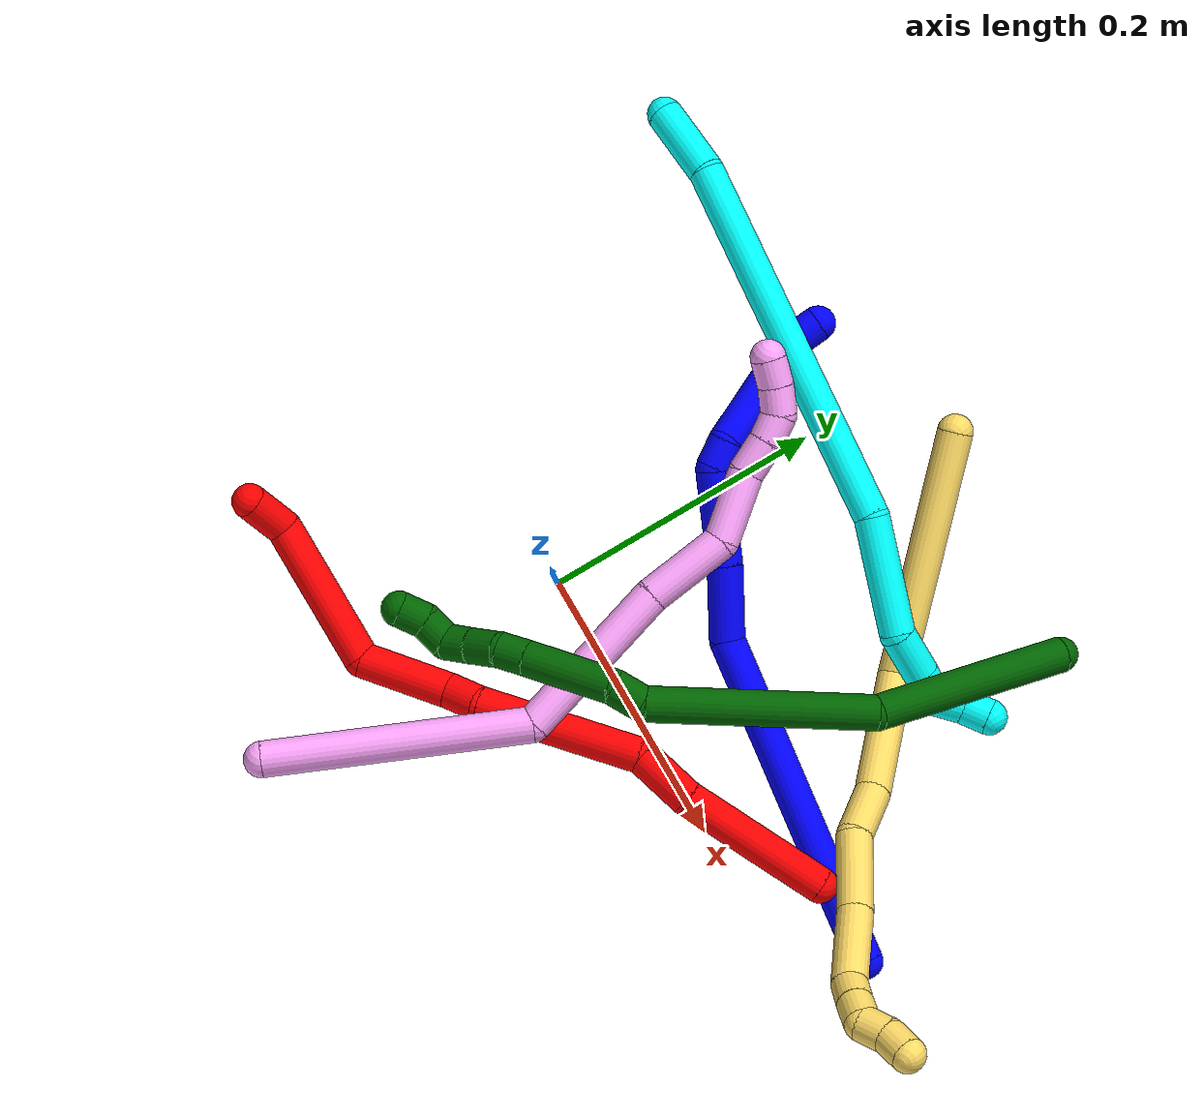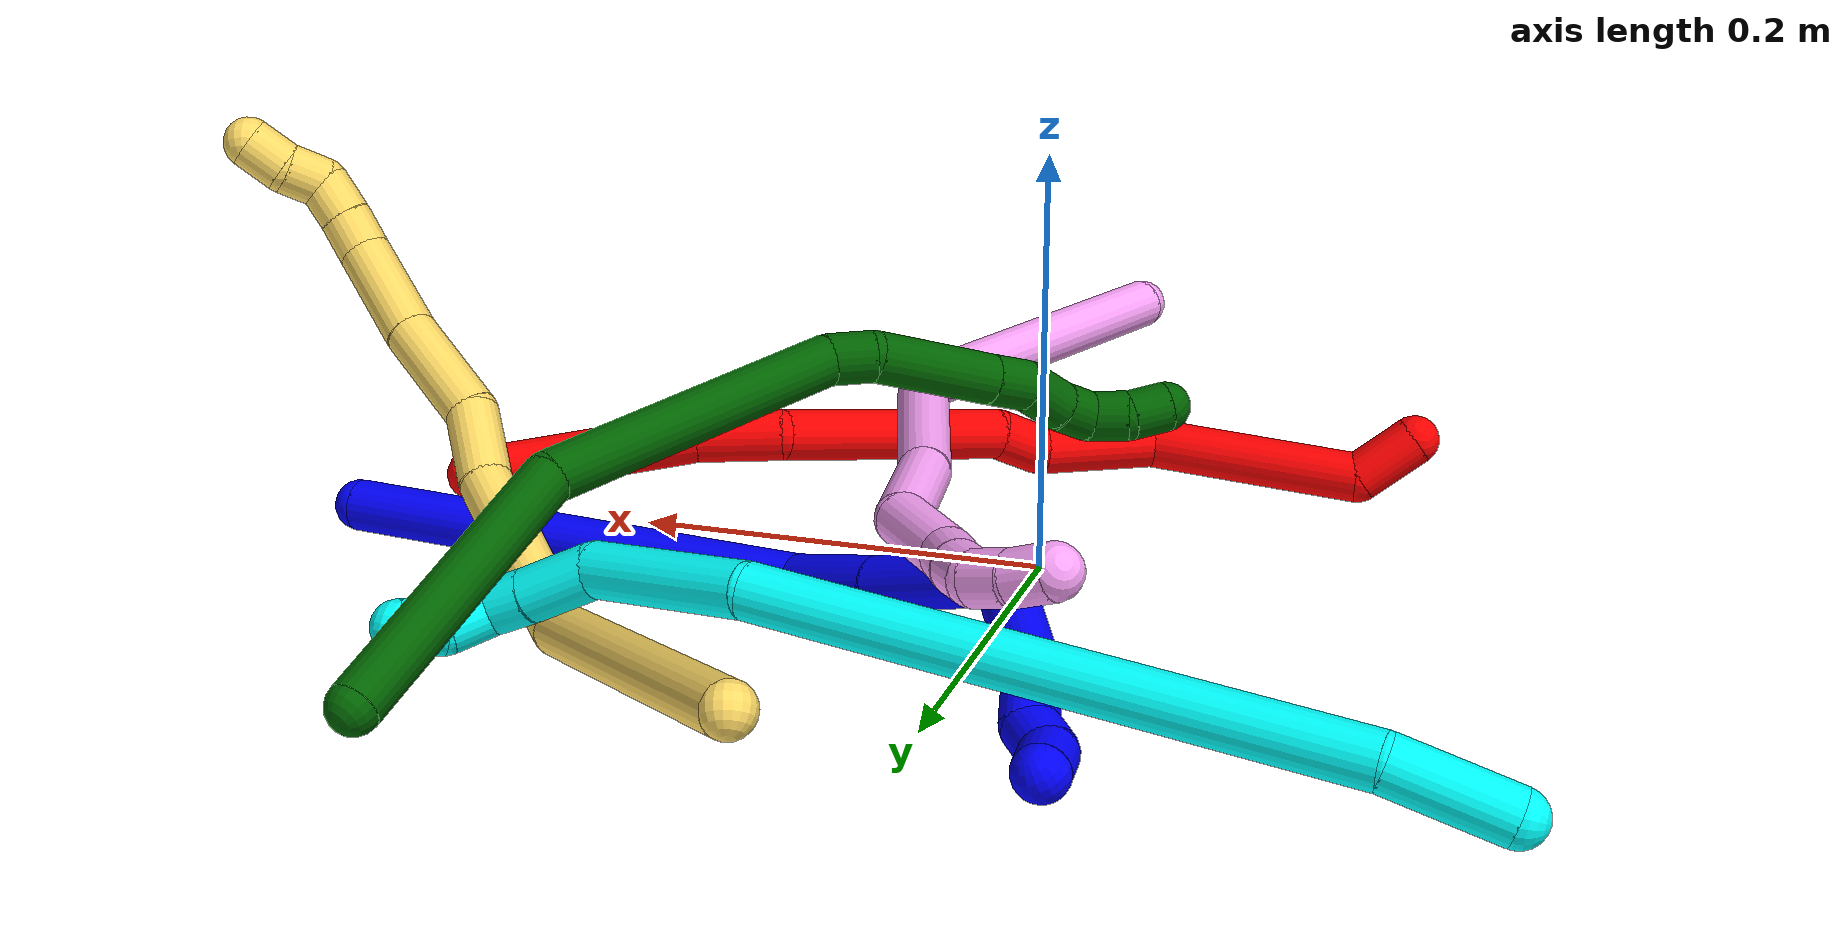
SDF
<sdf version="1.7">
 <world name="default">
  <plugin name="TubeGeneratorPlugin" filename="libtube_generator_plugin.so"/>
  <model name="photoneo_s_sensor">
   <static>1</static>
   <pose>0 0 2 1.57079 1.57079 3.14159</pose>
   <link name="link">
    <inertial><mass>0.1</mass></inertial>
    <sensor name="sensor" type="depth">
     <update_rate>30</update_rate>
     <camera>
      <horizontal_fov>1.22</horizontal_fov>
      <image><width>1920</width><height>1200</height><format>B8G8R8</format></image>
      <clip><near>0.1</near><far>4</far></clip>
      <depth_camera><output>points</output></depth_camera>
     </camera>
     <plugin name="camera_plugin" filename="libgazebo_ros_depth_camera.so">
      <baseline>0.2</baseline>
      <alwaysOn>1</alwaysOn>
      <updateRate>0.0</updateRate>
      <cameraName>camera_ir</cameraName>
      <imageTopicName>/camera/color/image_raw</imageTopicName>
      <cameraInfoTopicName>/camera/color/camera_info</cameraInfoTopicName>
      <depthImageTopicName>/camera/depth/image_raw</depthImageTopicName>
      <depthImageCameraInfoTopicName>/camera/depth/camera_info</depthImageCameraInfoTopicName>
      <pointCloudTopicName>/camera/depth/points</pointCloudTopicName>
      <frameName>fr_optical</frameName>
      <pointCloudCutoff>0.1</pointCloudCutoff>
      <pointCloudCutoffMax>2.0</pointCloudCutoffMax>
      <distortionK1>0</distortionK1>
      <distortionK2>0</distortionK2>
      <distortionK3>0</distortionK3>
      <distortionT1>0</distortionT1>
      <distortionT2>0</distortionT2>
      <CxPrime>0</CxPrime>
      <Cx>0</Cx>
      <Cy>0</Cy>
      <focalLength>0</focalLength>
      <hackBaseline>0</hackBaseline>
     </plugin>
    </sensor>
   </link>
  </model>
  <gravity>0 0 -9.8</gravity>
  <magnetic_field>6e-06 2.3e-05 -4.2e-05</magnetic_field>
  <atmosphere type="adiabatic"/>
  <physics name="default_physics" default="0" type="ode">
   <max_step_size>0.003</max_step_size>
   <real_time_factor>1</real_time_factor>
   <real_time_update_rate>1000</real_time_update_rate>
   <max_contacts>10000</max_contacts>
   <ode>
    <solver>
     <type>quick</type>
     <iters>100</iters>
     <sor>1.3</sor>
     <use_dynamic_moi_rescaling>0</use_dynamic_moi_rescaling>
    </solver>
    <constraints>
     <contact_max_correcting_vel>0</contact_max_correcting_vel>
     <contact_surface_layer>0.001</contact_surface_layer>
     <cfm>0</cfm>
     <erp>0.2</erp>
    </constraints>
   </ode>
  </physics>
  <scene><ambient>0.4 0.4 0.4 1</ambient><background>0.7 0.7 0.7 1</background><shadows>0</shadows></scene>
  <audio><device>default</device></audio>
  <spherical_coordinates>
   <surface_model>EARTH_WGS84</surface_model>
   <latitude_deg>0</latitude_deg>
   <longitude_deg>0</longitude_deg>
   <elevation>0</elevation>
   <heading_deg>0</heading_deg>
  </spherical_coordinates>
  <model name="bin">
   <static>1</static>
   <link name="bottom">
    <collision name="collision-bottom">
     <pose>0 0 -0.01 0 -0 0</pose>
     <geometry><box><size>0.8 0.6 0.02</size></box></geometry>
     <surface>
      <friction><ode><mu>100</mu><mu2>100</mu2></ode></friction>
      <contact><collide_bitmask>65535</collide_bitmask></contact>
     </surface>
    </collision>
   </link>
   <link name="west_wall">
    <collision name="collision-west_wall">
     <pose>-0.41 0 0.1 0 -0 0</pose>
     <geometry><box><size>0.02 0.6 0.2</size></box></geometry>
     <surface>
      <friction><ode><mu>100</mu><mu2>100</mu2></ode></friction>
      <contact><collide_bitmask>65535</collide_bitmask></contact>
     </surface>
    </collision>
   </link>
   <link name="east_wall">
    <collision name="collision-east_wall">
     <pose>0.41 0 0.1 0 -0 0</pose>
     <geometry><box><size>0.02 0.6 0.2</size></box></geometry>
     <surface>
      <friction><ode><mu>100</mu><mu2>100</mu2></ode></friction>
      <contact><collide_bitmask>65535</collide_bitmask></contact>
     </surface>
    </collision>
   </link>
   <link name="south_wall">
    <collision name="collision-south_wall">
     <pose>0 -0.31 0.1 0 -0 0</pose>
     <geometry><box><size>0.8 0.02 0.2</size></box></geometry>
     <surface>
      <friction><ode><mu>100</mu><mu2>100</mu2></ode></friction>
      <contact><collide_bitmask>65535</collide_bitmask></contact>
     </surface>
    </collision>
   </link>
   <link name="north_wall">
    <collision name="collision-north_wall">
     <pose>0 0.31 0.1 0 -0 0</pose>
     <geometry><box><size>0.8 0.02 0.2</size></box></geometry>
     <surface>
      <friction><ode><mu>100</mu><mu2>100</mu2></ode></friction>
      <contact><collide_bitmask>65535</collide_bitmask></contact>
     </surface>
    </collision>
   </link>
  </model>
  <model name="1">
   <static>0</static>
   <link name="1">
    <collision name="collision-cylinder-e_1_1_4">
     <pose>-0.113392 0.005627 -0.039256 -2.99922 -1.23436 2.94131</pose>
     <geometry><cylinder><radius>0.0125</radius><length>0.240254</length></cylinder></geometry>
     <surface>
      <friction><ode><mu>1.16</mu><mu2>1.16</mu2><slip1>0</slip1><slip2>0</slip2></ode></friction>
      <contact><ode><kp>1e+06</kp><kd>1</kd><max_vel>0</max_vel><min_depth>0.001</min_depth></ode></contact>
     </surface>
    </collision>
    <visual name="visual-cylinder-e_1_1_4">
     <pose>-0.113392 0.005627 -0.039256 -2.99922 -1.23436 2.94131</pose>
     <geometry><cylinder><radius>0.0125</radius><length>0.240254</length></cylinder></geometry>
     <material><ambient>0 0 1 1</ambient></material>
    </visual>
    <collision name="collision-cylinder-e_2_4_5">
     <pose>-0.252729 0.018969 -0.07728 -1.41261 -1.27828 1.13015</pose>
     <geometry><cylinder><radius>0.0125</radius><length>0.05419</length></cylinder></geometry>
     <surface>
      <friction><ode><mu>1.16</mu><mu2>1.16</mu2><slip1>0</slip1><slip2>0</slip2></ode></friction>
      <contact><ode><kp>1e+06</kp><kd>1</kd><max_vel>0</max_vel><min_depth>0.001</min_depth></ode></contact>
     </surface>
    </collision>
    <visual name="visual-cylinder-e_2_4_5">
     <pose>-0.252729 0.018969 -0.07728 -1.41261 -1.27828 1.13015</pose>
     <geometry><cylinder><radius>0.0125</radius><length>0.05419</length></cylinder></geometry>
     <material><ambient>0 0 1 1</ambient></material>
    </visual>
    <collision name="collision-cylinder-e_3_5_6">
     <pose>-0.311589 0.033243 -0.07485 -1.3899 -1.37098 1.19678</pose>
     <geometry><cylinder><radius>0.0125</radius><length>0.067169</length></cylinder></geometry>
     <surface>
      <friction><ode><mu>1.16</mu><mu2>1.16</mu2><slip1>0</slip1><slip2>0</slip2></ode></friction>
      <contact><ode><kp>1e+06</kp><kd>1</kd><max_vel>0</max_vel><min_depth>0.001</min_depth></ode></contact>
     </surface>
    </collision>
    <visual name="visual-cylinder-e_3_5_6">
     <pose>-0.311589 0.033243 -0.07485 -1.3899 -1.37098 1.19678</pose>
     <geometry><cylinder><radius>0.0125</radius><length>0.067169</length></cylinder></geometry>
     <material><ambient>0 0 1 1</ambient></material>
    </visual>
    <collision name="collision-cylinder-e_4_6_7">
     <pose>-0.351685 0.047298 -0.072853 -1.46472 -0.760921 0.690444</pose>
     <geometry><cylinder><radius>0.0125</radius><length>0.020823</length></cylinder></geometry>
     <surface>
      <friction><ode><mu>1.16</mu><mu2>1.16</mu2><slip1>0</slip1><slip2>0</slip2></ode></friction>
      <contact><ode><kp>1e+06</kp><kd>1</kd><max_vel>0</max_vel><min_depth>0.001</min_depth></ode></contact>
     </surface>
    </collision>
    <visual name="visual-cylinder-e_4_6_7">
     <pose>-0.351685 0.047298 -0.072853 -1.46472 -0.760921 0.690444</pose>
     <geometry><cylinder><radius>0.0125</radius><length>0.020823</length></cylinder></geometry>
     <material><ambient>0 0 1 1</ambient></material>
    </visual>
    <collision name="collision-cylinder-e_5_7_8">
     <pose>-0.372227 0.078752 -0.075316 -1.70611 -0.504887 0.574542</pose>
     <geometry><cylinder><radius>0.0125</radius><length>0.055248</length></cylinder></geometry>
     <surface>
      <friction><ode><mu>1.16</mu><mu2>1.16</mu2><slip1>0</slip1><slip2>0</slip2></ode></friction>
      <contact><ode><kp>1e+06</kp><kd>1</kd><max_vel>0</max_vel><min_depth>0.001</min_depth></ode></contact>
     </surface>
    </collision>
    <visual name="visual-cylinder-e_5_7_8">
     <pose>-0.372227 0.078752 -0.075316 -1.70611 -0.504887 0.574542</pose>
     <geometry><cylinder><radius>0.0125</radius><length>0.055248</length></cylinder></geometry>
     <material><ambient>0 0 1 1</ambient></material>
    </visual>
    <collision name="collision-cylinder-e_6_8_9">
     <pose>-0.385665 0.112403 -0.084058 -2.08531 -0.006851 0.011742</pose>
     <geometry><cylinder><radius>0.0125</radius><length>0.022274</length></cylinder></geometry>
     <surface>
      <friction><ode><mu>1.16</mu><mu2>1.16</mu2><slip1>0</slip1><slip2>0</slip2></ode></friction>
      <contact><ode><kp>1e+06</kp><kd>1</kd><max_vel>0</max_vel><min_depth>0.001</min_depth></ode></contact>
     </surface>
    </collision>
    <visual name="visual-cylinder-e_6_8_9">
     <pose>-0.385665 0.112403 -0.084058 -2.08531 -0.006851 0.011742</pose>
     <geometry><cylinder><radius>0.0125</radius><length>0.022274</length></cylinder></geometry>
     <material><ambient>0 0 1 1</ambient></material>
    </visual>
    <collision name="collision-cylinder-e_7_9_10">
     <pose>-0.392292 0.129453 -0.091319 -1.8083 -0.713495 0.884738</pose>
     <geometry><cylinder><radius>0.0125</radius><length>0.020017</length></cylinder></geometry>
     <surface>
      <friction><ode><mu>1.16</mu><mu2>1.16</mu2><slip1>0</slip1><slip2>0</slip2></ode></friction>
      <contact><ode><kp>1e+06</kp><kd>1</kd><max_vel>0</max_vel><min_depth>0.001</min_depth></ode></contact>
     </surface>
    </collision>
    <visual name="visual-cylinder-e_7_9_10">
     <pose>-0.392292 0.129453 -0.091319 -1.8083 -0.713495 0.884738</pose>
     <geometry><cylinder><radius>0.0125</radius><length>0.020017</length></cylinder></geometry>
     <material><ambient>0 0 1 1</ambient></material>
    </visual>
    <collision name="collision-cylinder-e_8_10_2">
     <pose>-0.401638 0.145985 -0.090235 -1.26834 -0.283036 0.208818</pose>
     <geometry><cylinder><radius>0.0125</radius><length>0.020025</length></cylinder></geometry>
     <surface>
      <friction><ode><mu>1.16</mu><mu2>1.16</mu2><slip1>0</slip1><slip2>0</slip2></ode></friction>
      <contact><ode><kp>1e+06</kp><kd>1</kd><max_vel>0</max_vel><min_depth>0.001</min_depth></ode></contact>
     </surface>
    </collision>
    <visual name="visual-cylinder-e_8_10_2">
     <pose>-0.401638 0.145985 -0.090235 -1.26834 -0.283036 0.208818</pose>
     <geometry><cylinder><radius>0.0125</radius><length>0.020025</length></cylinder></geometry>
     <material><ambient>0 0 1 1</ambient></material>
    </visual>
    <collision name="collision-sphere-2">
     <pose>-0.404435 0.155163 -0.087372 0 -0 0</pose>
     <geometry><sphere><radius>0.0125</radius></sphere></geometry>
     <surface>
      <friction><ode><mu>1.16</mu><mu2>1.16</mu2><slip1>0</slip1><slip2>0</slip2></ode></friction>
      <contact><ode><kp>1e+06</kp><kd>1</kd><max_vel>0</max_vel><min_depth>0.001</min_depth></ode></contact>
     </surface>
    </collision>
    <visual name="visual-sphere-2">
     <pose>-0.404435 0.155163 -0.087372 0 -0 0</pose>
     <geometry><sphere><radius>0.0125</radius></sphere></geometry>
     <material><ambient>0 0 1 1</ambient></material>
    </visual>
    <collision name="collision-sphere-10">
     <pose>-0.398842 0.136807 -0.093099 0 -0 0</pose>
     <geometry><sphere><radius>0.0125</radius></sphere></geometry>
     <surface>
      <friction><ode><mu>1.16</mu><mu2>1.16</mu2><slip1>0</slip1><slip2>0</slip2></ode></friction>
      <contact><ode><kp>1e+06</kp><kd>1</kd><max_vel>0</max_vel><min_depth>0.001</min_depth></ode></contact>
     </surface>
    </collision>
    <visual name="visual-sphere-10">
     <pose>-0.398842 0.136807 -0.093099 0 -0 0</pose>
     <geometry><sphere><radius>0.0125</radius></sphere></geometry>
     <material><ambient>0 0 1 1</ambient></material>
    </visual>
    <collision name="collision-sphere-9">
     <pose>-0.385742 0.122098 -0.089538 0 -0 0</pose>
     <geometry><sphere><radius>0.0125</radius></sphere></geometry>
     <surface>
      <friction><ode><mu>1.16</mu><mu2>1.16</mu2><slip1>0</slip1><slip2>0</slip2></ode></friction>
      <contact><ode><kp>1e+06</kp><kd>1</kd><max_vel>0</max_vel><min_depth>0.001</min_depth></ode></contact>
     </surface>
    </collision>
    <visual name="visual-sphere-9">
     <pose>-0.385742 0.122098 -0.089538 0 -0 0</pose>
     <geometry><sphere><radius>0.0125</radius></sphere></geometry>
     <material><ambient>0 0 1 1</ambient></material>
    </visual>
    <collision name="collision-sphere-4">
     <pose>-0.226785 0.011254 -0.078511 0 -0 0</pose>
     <geometry><sphere><radius>0.0125</radius></sphere></geometry>
     <surface>
      <friction><ode><mu>1.16</mu><mu2>1.16</mu2><slip1>0</slip1><slip2>0</slip2></ode></friction>
      <contact><ode><kp>1e+06</kp><kd>1</kd><max_vel>0</max_vel><min_depth>0.001</min_depth></ode></contact>
     </surface>
    </collision>
    <visual name="visual-sphere-4">
     <pose>-0.226785 0.011254 -0.078511 0 -0 0</pose>
     <geometry><sphere><radius>0.0125</radius></sphere></geometry>
     <material><ambient>0 0 1 1</ambient></material>
    </visual>
    <collision name="collision-sphere-1">
     <geometry><sphere><radius>0.0125</radius></sphere></geometry>
     <surface>
      <friction><ode><mu>1.16</mu><mu2>1.16</mu2><slip1>0</slip1><slip2>0</slip2></ode></friction>
      <contact><ode><kp>1e+06</kp><kd>1</kd><max_vel>0</max_vel><min_depth>0.001</min_depth></ode></contact>
     </surface>
    </collision>
    <visual name="visual-sphere-1">
     <geometry><sphere><radius>0.0125</radius></sphere></geometry>
     <material><ambient>0 0 1 1</ambient></material>
    </visual>
    <collision name="collision-sphere-8">
     <pose>-0.385589 0.102708 -0.078577 0 -0 0</pose>
     <geometry><sphere><radius>0.0125</radius></sphere></geometry>
     <surface>
      <friction><ode><mu>1.16</mu><mu2>1.16</mu2><slip1>0</slip1><slip2>0</slip2></ode></friction>
      <contact><ode><kp>1e+06</kp><kd>1</kd><max_vel>0</max_vel><min_depth>0.001</min_depth></ode></contact>
     </surface>
    </collision>
    <visual name="visual-sphere-8">
     <pose>-0.385589 0.102708 -0.078577 0 -0 0</pose>
     <geometry><sphere><radius>0.0125</radius></sphere></geometry>
     <material><ambient>0 0 1 1</ambient></material>
    </visual>
    <collision name="collision-sphere-5">
     <pose>-0.278673 0.026685 -0.07605 0 -0 0</pose>
     <geometry><sphere><radius>0.0125</radius></sphere></geometry>
     <surface>
      <friction><ode><mu>1.16</mu><mu2>1.16</mu2><slip1>0</slip1><slip2>0</slip2></ode></friction>
      <contact><ode><kp>1e+06</kp><kd>1</kd><max_vel>0</max_vel><min_depth>0.001</min_depth></ode></contact>
     </surface>
    </collision>
    <visual name="visual-sphere-5">
     <pose>-0.278673 0.026685 -0.07605 0 -0 0</pose>
     <geometry><sphere><radius>0.0125</radius></sphere></geometry>
     <material><ambient>0 0 1 1</ambient></material>
    </visual>
    <collision name="collision-sphere-6">
     <pose>-0.344506 0.0398 -0.073651 0 -0 0</pose>
     <geometry><sphere><radius>0.0125</radius></sphere></geometry>
     <surface>
      <friction><ode><mu>1.16</mu><mu2>1.16</mu2><slip1>0</slip1><slip2>0</slip2></ode></friction>
      <contact><ode><kp>1e+06</kp><kd>1</kd><max_vel>0</max_vel><min_depth>0.001</min_depth></ode></contact>
     </surface>
    </collision>
    <visual name="visual-sphere-6">
     <pose>-0.344506 0.0398 -0.073651 0 -0 0</pose>
     <geometry><sphere><radius>0.0125</radius></sphere></geometry>
     <material><ambient>0 0 1 1</ambient></material>
    </visual>
    <collision name="collision-sphere-7">
     <pose>-0.358865 0.054796 -0.072054 0 -0 0</pose>
     <geometry><sphere><radius>0.0125</radius></sphere></geometry>
     <surface>
      <friction><ode><mu>1.16</mu><mu2>1.16</mu2><slip1>0</slip1><slip2>0</slip2></ode></friction>
      <contact><ode><kp>1e+06</kp><kd>1</kd><max_vel>0</max_vel><min_depth>0.001</min_depth></ode></contact>
     </surface>
    </collision>
    <visual name="visual-sphere-7">
     <pose>-0.358865 0.054796 -0.072054 0 -0 0</pose>
     <geometry><sphere><radius>0.0125</radius></sphere></geometry>
     <material><ambient>0 0 1 1</ambient></material>
    </visual>
    <inertial>
     <pose>-0.228482 0.035933 -0.059664 0 -0 0</pose>
     <mass>0.5</mass>
     <inertia>
      <ixx>-0.000293</ixx>
      <ixy>0</ixy>
      <ixz>0</ixz>
      <iyy>0.001313</iyy>
      <iyz>0</iyz>
      <izz>0.001062</izz>
     </inertia>
    </inertial>
   </link>
   <pose>0.332277 0.050065 0.011498 -0.366909 0.328596 -0.201653</pose>
  </model>
  <model name="2">
   <static>0</static>
   <link name="2">
    <collision name="collision-cylinder-e_1_1_4">
     <pose>0.008367 0.011527 -0.009245 -2.24677 0.515253 -1.00426</pose>
     <geometry><cylinder><radius>0.0125</radius><length>0.033962</length></cylinder></geometry>
     <surface>
      <friction><ode><mu>1.16</mu><mu2>1.16</mu2><slip1>0</slip1><slip2>0</slip2></ode></friction>
      <contact><ode><kp>1e+06</kp><kd>1</kd><max_vel>0</max_vel><min_depth>0.001</min_depth></ode></contact>
     </surface>
    </collision>
    <visual name="visual-cylinder-e_1_1_4">
     <pose>0.008367 0.011527 -0.009245 -2.24677 0.515253 -1.00426</pose>
     <geometry><cylinder><radius>0.0125</radius><length>0.033962</length></cylinder></geometry>
     <material><ambient>1 0 0 1</ambient></material>
    </visual>
    <collision name="collision-cylinder-e_2_4_5">
     <pose>0.067534 0.030327 -0.033632 -2.69379 1.25144 -2.531</pose>
     <geometry><cylinder><radius>0.0125</radius><length>0.107009</length></cylinder></geometry>
     <surface>
      <friction><ode><mu>1.16</mu><mu2>1.16</mu2><slip1>0</slip1><slip2>0</slip2></ode></friction>
      <contact><ode><kp>1e+06</kp><kd>1</kd><max_vel>0</max_vel><min_depth>0.001</min_depth></ode></contact>
     </surface>
    </collision>
    <visual name="visual-cylinder-e_2_4_5">
     <pose>0.067534 0.030327 -0.033632 -2.69379 1.25144 -2.531</pose>
     <geometry><cylinder><radius>0.0125</radius><length>0.107009</length></cylinder></geometry>
     <material><ambient>1 0 0 1</ambient></material>
    </visual>
    <collision name="collision-cylinder-e_3_5_6">
     <pose>0.142792 0.057993 -0.044683 -1.37284 0.866083 -0.724171</pose>
     <geometry><cylinder><radius>0.0125</radius><length>0.064213</length></cylinder></geometry>
     <surface>
      <friction><ode><mu>1.16</mu><mu2>1.16</mu2><slip1>0</slip1><slip2>0</slip2></ode></friction>
      <contact><ode><kp>1e+06</kp><kd>1</kd><max_vel>0</max_vel><min_depth>0.001</min_depth></ode></contact>
     </surface>
    </collision>
    <visual name="visual-cylinder-e_3_5_6">
     <pose>0.142792 0.057993 -0.044683 -1.37284 0.866083 -0.724171</pose>
     <geometry><cylinder><radius>0.0125</radius><length>0.064213</length></cylinder></geometry>
     <material><ambient>1 0 0 1</ambient></material>
    </visual>
    <collision name="collision-cylinder-e_4_6_7">
     <pose>0.1782 0.082837 -0.036155 -0.786871 1.04969 -0.471725</pose>
     <geometry><cylinder><radius>0.0125</radius><length>0.02525</length></cylinder></geometry>
     <surface>
      <friction><ode><mu>1.16</mu><mu2>1.16</mu2><slip1>0</slip1><slip2>0</slip2></ode></friction>
      <contact><ode><kp>1e+06</kp><kd>1</kd><max_vel>0</max_vel><min_depth>0.001</min_depth></ode></contact>
     </surface>
    </collision>
    <visual name="visual-cylinder-e_4_6_7">
     <pose>0.1782 0.082837 -0.036155 -0.786871 1.04969 -0.471725</pose>
     <geometry><cylinder><radius>0.0125</radius><length>0.02525</length></cylinder></geometry>
     <material><ambient>1 0 0 1</ambient></material>
    </visual>
    <collision name="collision-cylinder-e_5_7_8">
     <pose>0.234054 0.123471 -0.020291 -1.26491 0.869218 -0.655857</pose>
     <geometry><cylinder><radius>0.0125</radius><length>0.11758</length></cylinder></geometry>
     <surface>
      <friction><ode><mu>1.16</mu><mu2>1.16</mu2><slip1>0</slip1><slip2>0</slip2></ode></friction>
      <contact><ode><kp>1e+06</kp><kd>1</kd><max_vel>0</max_vel><min_depth>0.001</min_depth></ode></contact>
     </surface>
    </collision>
    <visual name="visual-cylinder-e_5_7_8">
     <pose>0.234054 0.123471 -0.020291 -1.26491 0.869218 -0.655857</pose>
     <geometry><cylinder><radius>0.0125</radius><length>0.11758</length></cylinder></geometry>
     <material><ambient>1 0 0 1</ambient></material>
    </visual>
    <collision name="collision-cylinder-e_6_8_9">
     <pose>0.297774 0.168598 -0.013191 -2.02139 1.08494 -1.53128</pose>
     <geometry><cylinder><radius>0.0125</radius><length>0.042553</length></cylinder></geometry>
     <surface>
      <friction><ode><mu>1.16</mu><mu2>1.16</mu2><slip1>0</slip1><slip2>0</slip2></ode></friction>
      <contact><ode><kp>1e+06</kp><kd>1</kd><max_vel>0</max_vel><min_depth>0.001</min_depth></ode></contact>
     </surface>
    </collision>
    <visual name="visual-cylinder-e_6_8_9">
     <pose>0.297774 0.168598 -0.013191 -2.02139 1.08494 -1.53128</pose>
     <geometry><cylinder><radius>0.0125</radius><length>0.042553</length></cylinder></geometry>
     <material><ambient>1 0 0 1</ambient></material>
    </visual>
    <collision name="collision-cylinder-e_7_9_2">
     <pose>0.359979 0.209593 -0.026673 -1.84902 0.915744 -1.15734</pose>
     <geometry><cylinder><radius>0.0125</radius><length>0.109434</length></cylinder></geometry>
     <surface>
      <friction><ode><mu>1.16</mu><mu2>1.16</mu2><slip1>0</slip1><slip2>0</slip2></ode></friction>
      <contact><ode><kp>1e+06</kp><kd>1</kd><max_vel>0</max_vel><min_depth>0.001</min_depth></ode></contact>
     </surface>
    </collision>
    <visual name="visual-cylinder-e_7_9_2">
     <pose>0.359979 0.209593 -0.026673 -1.84902 0.915744 -1.15734</pose>
     <geometry><cylinder><radius>0.0125</radius><length>0.109434</length></cylinder></geometry>
     <material><ambient>1 0 0 1</ambient></material>
    </visual>
    <collision name="collision-sphere-2">
     <pose>0.40337 0.241645 -0.035828 0 -0 0</pose>
     <geometry><sphere><radius>0.0125</radius></sphere></geometry>
     <surface>
      <friction><ode><mu>1.16</mu><mu2>1.16</mu2><slip1>0</slip1><slip2>0</slip2></ode></friction>
      <contact><ode><kp>1e+06</kp><kd>1</kd><max_vel>0</max_vel><min_depth>0.001</min_depth></ode></contact>
     </surface>
    </collision>
    <visual name="visual-sphere-2">
     <pose>0.40337 0.241645 -0.035828 0 -0 0</pose>
     <geometry><sphere><radius>0.0125</radius></sphere></geometry>
     <material><ambient>1 0 0 1</ambient></material>
    </visual>
    <collision name="collision-sphere-9">
     <pose>0.316588 0.177541 -0.017518 0 -0 0</pose>
     <geometry><sphere><radius>0.0125</radius></sphere></geometry>
     <surface>
      <friction><ode><mu>1.16</mu><mu2>1.16</mu2><slip1>0</slip1><slip2>0</slip2></ode></friction>
      <contact><ode><kp>1e+06</kp><kd>1</kd><max_vel>0</max_vel><min_depth>0.001</min_depth></ode></contact>
     </surface>
    </collision>
    <visual name="visual-sphere-9">
     <pose>0.316588 0.177541 -0.017518 0 -0 0</pose>
     <geometry><sphere><radius>0.0125</radius></sphere></geometry>
     <material><ambient>1 0 0 1</ambient></material>
    </visual>
    <collision name="collision-sphere-4">
     <pose>0.016735 0.023054 -0.01849 0 -0 0</pose>
     <geometry><sphere><radius>0.0125</radius></sphere></geometry>
     <surface>
      <friction><ode><mu>1.16</mu><mu2>1.16</mu2><slip1>0</slip1><slip2>0</slip2></ode></friction>
      <contact><ode><kp>1e+06</kp><kd>1</kd><max_vel>0</max_vel><min_depth>0.001</min_depth></ode></contact>
     </surface>
    </collision>
    <visual name="visual-sphere-4">
     <pose>0.016735 0.023054 -0.01849 0 -0 0</pose>
     <geometry><sphere><radius>0.0125</radius></sphere></geometry>
     <material><ambient>1 0 0 1</ambient></material>
    </visual>
    <collision name="collision-sphere-1">
     <geometry><sphere><radius>0.0125</radius></sphere></geometry>
     <surface>
      <friction><ode><mu>1.16</mu><mu2>1.16</mu2><slip1>0</slip1><slip2>0</slip2></ode></friction>
      <contact><ode><kp>1e+06</kp><kd>1</kd><max_vel>0</max_vel><min_depth>0.001</min_depth></ode></contact>
     </surface>
    </collision>
    <visual name="visual-sphere-1">
     <geometry><sphere><radius>0.0125</radius></sphere></geometry>
     <material><ambient>1 0 0 1</ambient></material>
    </visual>
    <collision name="collision-sphere-8">
     <pose>0.27896 0.159654 -0.008864 0 -0 0</pose>
     <geometry><sphere><radius>0.0125</radius></sphere></geometry>
     <surface>
      <friction><ode><mu>1.16</mu><mu2>1.16</mu2><slip1>0</slip1><slip2>0</slip2></ode></friction>
      <contact><ode><kp>1e+06</kp><kd>1</kd><max_vel>0</max_vel><min_depth>0.001</min_depth></ode></contact>
     </surface>
    </collision>
    <visual name="visual-sphere-8">
     <pose>0.27896 0.159654 -0.008864 0 -0 0</pose>
     <geometry><sphere><radius>0.0125</radius></sphere></geometry>
     <material><ambient>1 0 0 1</ambient></material>
    </visual>
    <collision name="collision-sphere-5">
     <pose>0.118334 0.037601 -0.048773 0 -0 0</pose>
     <geometry><sphere><radius>0.0125</radius></sphere></geometry>
     <surface>
      <friction><ode><mu>1.16</mu><mu2>1.16</mu2><slip1>0</slip1><slip2>0</slip2></ode></friction>
      <contact><ode><kp>1e+06</kp><kd>1</kd><max_vel>0</max_vel><min_depth>0.001</min_depth></ode></contact>
     </surface>
    </collision>
    <visual name="visual-sphere-5">
     <pose>0.118334 0.037601 -0.048773 0 -0 0</pose>
     <geometry><sphere><radius>0.0125</radius></sphere></geometry>
     <material><ambient>1 0 0 1</ambient></material>
    </visual>
    <collision name="collision-sphere-6">
     <pose>0.167251 0.078386 -0.040593 0 -0 0</pose>
     <geometry><sphere><radius>0.0125</radius></sphere></geometry>
     <surface>
      <friction><ode><mu>1.16</mu><mu2>1.16</mu2><slip1>0</slip1><slip2>0</slip2></ode></friction>
      <contact><ode><kp>1e+06</kp><kd>1</kd><max_vel>0</max_vel><min_depth>0.001</min_depth></ode></contact>
     </surface>
    </collision>
    <visual name="visual-sphere-6">
     <pose>0.167251 0.078386 -0.040593 0 -0 0</pose>
     <geometry><sphere><radius>0.0125</radius></sphere></geometry>
     <material><ambient>1 0 0 1</ambient></material>
    </visual>
    <collision name="collision-sphere-7">
     <pose>0.189149 0.087288 -0.031717 0 -0 0</pose>
     <geometry><sphere><radius>0.0125</radius></sphere></geometry>
     <surface>
      <friction><ode><mu>1.16</mu><mu2>1.16</mu2><slip1>0</slip1><slip2>0</slip2></ode></friction>
      <contact><ode><kp>1e+06</kp><kd>1</kd><max_vel>0</max_vel><min_depth>0.001</min_depth></ode></contact>
     </surface>
    </collision>
    <visual name="visual-sphere-7">
     <pose>0.189149 0.087288 -0.031717 0 -0 0</pose>
     <geometry><sphere><radius>0.0125</radius></sphere></geometry>
     <material><ambient>1 0 0 1</ambient></material>
    </visual>
    <inertial>
     <pose>0.201529 0.108162 -0.027122 0 -0 0</pose>
     <mass>0.5</mass>
     <inertia>
      <ixx>-3.7e-05</ixx>
      <ixy>0</ixy>
      <ixz>0</ixz>
      <iyy>0.000153</iyy>
      <iyz>0</iyz>
      <izz>-0.000521</izz>
     </inertia>
    </inertial>
   </link>
   <pose>-0.154622 -0.153998 0.031122 -0.58865 -0.392693 0.052318</pose>
  </model>
  <model name="3">
   <static>0</static>
   <link name="3">
    <collision name="collision-cylinder-e_1_1_4">
     <pose>-0.002342 -0.003995 0.026453 0.149885 -0.087331 -0.006561</pose>
     <geometry><cylinder><radius>0.0125</radius><length>0.05371</length></cylinder></geometry>
     <surface>
      <friction><ode><mu>1.16</mu><mu2>1.16</mu2><slip1>0</slip1><slip2>0</slip2></ode></friction>
      <contact><ode><kp>1e+06</kp><kd>1</kd><max_vel>0</max_vel><min_depth>0.001</min_depth></ode></contact>
     </surface>
    </collision>
    <visual name="visual-cylinder-e_1_1_4">
     <pose>-0.002342 -0.003995 0.026453 0.149885 -0.087331 -0.006561</pose>
     <geometry><cylinder><radius>0.0125</radius><length>0.05371</length></cylinder></geometry>
     <material><ambient>0.003922 1 0.996078 1</ambient></material>
    </visual>
    <collision name="collision-cylinder-e_2_4_5">
     <pose>0.014956 -0.010882 0.185137 0.02187 0.147422 0.001615</pose>
     <geometry><cylinder><radius>0.0125</radius><length>0.267428</length></cylinder></geometry>
     <surface>
      <friction><ode><mu>1.16</mu><mu2>1.16</mu2><slip1>0</slip1><slip2>0</slip2></ode></friction>
      <contact><ode><kp>1e+06</kp><kd>1</kd><max_vel>0</max_vel><min_depth>0.001</min_depth></ode></contact>
     </surface>
    </collision>
    <visual name="visual-cylinder-e_2_4_5">
     <pose>0.014956 -0.010882 0.185137 0.02187 0.147422 0.001615</pose>
     <geometry><cylinder><radius>0.0125</radius><length>0.267428</length></cylinder></geometry>
     <material><ambient>0.003922 1 0.996078 1</ambient></material>
    </visual>
    <collision name="collision-cylinder-e_3_5_6">
     <pose>0.051851 -0.010716 0.354505 -0.082171 0.433649 -0.018111</pose>
     <geometry><cylinder><radius>0.0125</radius><length>0.082126</length></cylinder></geometry>
     <surface>
      <friction><ode><mu>1.16</mu><mu2>1.16</mu2><slip1>0</slip1><slip2>0</slip2></ode></friction>
      <contact><ode><kp>1e+06</kp><kd>1</kd><max_vel>0</max_vel><min_depth>0.001</min_depth></ode></contact>
     </surface>
    </collision>
    <visual name="visual-cylinder-e_3_5_6">
     <pose>0.051851 -0.010716 0.354505 -0.082171 0.433649 -0.018111</pose>
     <geometry><cylinder><radius>0.0125</radius><length>0.082126</length></cylinder></geometry>
     <material><ambient>0.003922 1 0.996078 1</ambient></material>
    </visual>
    <collision name="collision-cylinder-e_4_6_7">
     <pose>0.073345 0.001081 0.405687 -0.556521 0.25089 -0.072019</pose>
     <geometry><cylinder><radius>0.0125</radius><length>0.034154</length></cylinder></geometry>
     <surface>
      <friction><ode><mu>1.16</mu><mu2>1.16</mu2><slip1>0</slip1><slip2>0</slip2></ode></friction>
      <contact><ode><kp>1e+06</kp><kd>1</kd><max_vel>0</max_vel><min_depth>0.001</min_depth></ode></contact>
     </surface>
    </collision>
    <visual name="visual-cylinder-e_4_6_7">
     <pose>0.073345 0.001081 0.405687 -0.556521 0.25089 -0.072019</pose>
     <geometry><cylinder><radius>0.0125</radius><length>0.034154</length></cylinder></geometry>
     <material><ambient>0.003922 1 0.996078 1</ambient></material>
    </visual>
    <collision name="collision-cylinder-e_5_7_8">
     <pose>0.080434 0.014571 0.428564 -0.493674 0.276869 -0.070185</pose>
     <geometry><cylinder><radius>0.0125</radius><length>0.020851</length></cylinder></geometry>
     <surface>
      <friction><ode><mu>1.16</mu><mu2>1.16</mu2><slip1>0</slip1><slip2>0</slip2></ode></friction>
      <contact><ode><kp>1e+06</kp><kd>1</kd><max_vel>0</max_vel><min_depth>0.001</min_depth></ode></contact>
     </surface>
    </collision>
    <visual name="visual-cylinder-e_5_7_8">
     <pose>0.080434 0.014571 0.428564 -0.493674 0.276869 -0.070185</pose>
     <geometry><cylinder><radius>0.0125</radius><length>0.020851</length></cylinder></geometry>
     <material><ambient>0.003922 1 0.996078 1</ambient></material>
    </visual>
    <collision name="collision-cylinder-e_6_8_9">
     <pose>0.078575 0.025747 0.444765 -0.716939 -0.448884 0.170644</pose>
     <geometry><cylinder><radius>0.0125</radius><length>0.021704</length></cylinder></geometry>
     <surface>
      <friction><ode><mu>1.16</mu><mu2>1.16</mu2><slip1>0</slip1><slip2>0</slip2></ode></friction>
      <contact><ode><kp>1e+06</kp><kd>1</kd><max_vel>0</max_vel><min_depth>0.001</min_depth></ode></contact>
     </surface>
    </collision>
    <visual name="visual-cylinder-e_6_8_9">
     <pose>0.078575 0.025747 0.444765 -0.716939 -0.448884 0.170644</pose>
     <geometry><cylinder><radius>0.0125</radius><length>0.021704</length></cylinder></geometry>
     <material><ambient>0.003922 1 0.996078 1</ambient></material>
    </visual>
    <collision name="collision-cylinder-e_7_9_2">
     <pose>0.068927 0.034461 0.460541 -0.265892 -0.515671 0.070504</pose>
     <geometry><cylinder><radius>0.0125</radius><length>0.020028</length></cylinder></geometry>
     <surface>
      <friction><ode><mu>1.16</mu><mu2>1.16</mu2><slip1>0</slip1><slip2>0</slip2></ode></friction>
      <contact><ode><kp>1e+06</kp><kd>1</kd><max_vel>0</max_vel><min_depth>0.001</min_depth></ode></contact>
     </surface>
    </collision>
    <visual name="visual-cylinder-e_7_9_2">
     <pose>0.068927 0.034461 0.460541 -0.265892 -0.515671 0.070504</pose>
     <geometry><cylinder><radius>0.0125</radius><length>0.020028</length></cylinder></geometry>
     <material><ambient>0.003922 1 0.996078 1</ambient></material>
    </visual>
    <collision name="collision-sphere-2">
     <pose>0.063989 0.03675 0.468947 0 -0 0</pose>
     <geometry><sphere><radius>0.0125</radius></sphere></geometry>
     <surface>
      <friction><ode><mu>1.16</mu><mu2>1.16</mu2><slip1>0</slip1><slip2>0</slip2></ode></friction>
      <contact><ode><kp>1e+06</kp><kd>1</kd><max_vel>0</max_vel><min_depth>0.001</min_depth></ode></contact>
     </surface>
    </collision>
    <visual name="visual-sphere-2">
     <pose>0.063989 0.03675 0.468947 0 -0 0</pose>
     <geometry><sphere><radius>0.0125</radius></sphere></geometry>
     <material><ambient>0.003922 1 0.996078 1</ambient></material>
    </visual>
    <collision name="collision-sphere-9">
     <pose>0.073865 0.032172 0.452135 0 -0 0</pose>
     <geometry><sphere><radius>0.0125</radius></sphere></geometry>
     <surface>
      <friction><ode><mu>1.16</mu><mu2>1.16</mu2><slip1>0</slip1><slip2>0</slip2></ode></friction>
      <contact><ode><kp>1e+06</kp><kd>1</kd><max_vel>0</max_vel><min_depth>0.001</min_depth></ode></contact>
     </surface>
    </collision>
    <visual name="visual-sphere-9">
     <pose>0.073865 0.032172 0.452135 0 -0 0</pose>
     <geometry><sphere><radius>0.0125</radius></sphere></geometry>
     <material><ambient>0.003922 1 0.996078 1</ambient></material>
    </visual>
    <collision name="collision-sphere-4">
     <pose>-0.004685 -0.00799 0.052905 0 -0 0</pose>
     <geometry><sphere><radius>0.0125</radius></sphere></geometry>
     <surface>
      <friction><ode><mu>1.16</mu><mu2>1.16</mu2><slip1>0</slip1><slip2>0</slip2></ode></friction>
      <contact><ode><kp>1e+06</kp><kd>1</kd><max_vel>0</max_vel><min_depth>0.001</min_depth></ode></contact>
     </surface>
    </collision>
    <visual name="visual-sphere-4">
     <pose>-0.004685 -0.00799 0.052905 0 -0 0</pose>
     <geometry><sphere><radius>0.0125</radius></sphere></geometry>
     <material><ambient>0.003922 1 0.996078 1</ambient></material>
    </visual>
    <collision name="collision-sphere-1">
     <geometry><sphere><radius>0.0125</radius></sphere></geometry>
     <surface>
      <friction><ode><mu>1.16</mu><mu2>1.16</mu2><slip1>0</slip1><slip2>0</slip2></ode></friction>
      <contact><ode><kp>1e+06</kp><kd>1</kd><max_vel>0</max_vel><min_depth>0.001</min_depth></ode></contact>
     </surface>
    </collision>
    <visual name="visual-sphere-1">
     <geometry><sphere><radius>0.0125</radius></sphere></geometry>
     <material><ambient>0.003922 1 0.996078 1</ambient></material>
    </visual>
    <collision name="collision-sphere-8">
     <pose>0.083284 0.019323 0.437395 0 -0 0</pose>
     <geometry><sphere><radius>0.0125</radius></sphere></geometry>
     <surface>
      <friction><ode><mu>1.16</mu><mu2>1.16</mu2><slip1>0</slip1><slip2>0</slip2></ode></friction>
      <contact><ode><kp>1e+06</kp><kd>1</kd><max_vel>0</max_vel><min_depth>0.001</min_depth></ode></contact>
     </surface>
    </collision>
    <visual name="visual-sphere-8">
     <pose>0.083284 0.019323 0.437395 0 -0 0</pose>
     <geometry><sphere><radius>0.0125</radius></sphere></geometry>
     <material><ambient>0.003922 1 0.996078 1</ambient></material>
    </visual>
    <collision name="collision-sphere-5">
     <pose>0.034597 -0.013774 0.317369 0 -0 0</pose>
     <geometry><sphere><radius>0.0125</radius></sphere></geometry>
     <surface>
      <friction><ode><mu>1.16</mu><mu2>1.16</mu2><slip1>0</slip1><slip2>0</slip2></ode></friction>
      <contact><ode><kp>1e+06</kp><kd>1</kd><max_vel>0</max_vel><min_depth>0.001</min_depth></ode></contact>
     </surface>
    </collision>
    <visual name="visual-sphere-5">
     <pose>0.034597 -0.013774 0.317369 0 -0 0</pose>
     <geometry><sphere><radius>0.0125</radius></sphere></geometry>
     <material><ambient>0.003922 1 0.996078 1</ambient></material>
    </visual>
    <collision name="collision-sphere-6">
     <pose>0.069105 -0.007658 0.391641 0 -0 0</pose>
     <geometry><sphere><radius>0.0125</radius></sphere></geometry>
     <surface>
      <friction><ode><mu>1.16</mu><mu2>1.16</mu2><slip1>0</slip1><slip2>0</slip2></ode></friction>
      <contact><ode><kp>1e+06</kp><kd>1</kd><max_vel>0</max_vel><min_depth>0.001</min_depth></ode></contact>
     </surface>
    </collision>
    <visual name="visual-sphere-6">
     <pose>0.069105 -0.007658 0.391641 0 -0 0</pose>
     <geometry><sphere><radius>0.0125</radius></sphere></geometry>
     <material><ambient>0.003922 1 0.996078 1</ambient></material>
    </visual>
    <collision name="collision-sphere-7">
     <pose>0.077585 0.009819 0.419733 0 -0 0</pose>
     <geometry><sphere><radius>0.0125</radius></sphere></geometry>
     <surface>
      <friction><ode><mu>1.16</mu><mu2>1.16</mu2><slip1>0</slip1><slip2>0</slip2></ode></friction>
      <contact><ode><kp>1e+06</kp><kd>1</kd><max_vel>0</max_vel><min_depth>0.001</min_depth></ode></contact>
     </surface>
    </collision>
    <visual name="visual-sphere-7">
     <pose>0.077585 0.009819 0.419733 0 -0 0</pose>
     <geometry><sphere><radius>0.0125</radius></sphere></geometry>
     <material><ambient>0.003922 1 0.996078 1</ambient></material>
    </visual>
    <inertial>
     <pose>0.030801 -0.00483 0.243428 0 -0 0</pose>
     <mass>0.5</mass>
     <inertia>
      <ixx>0.001662</ixx>
      <ixy>0</ixy>
      <ixz>0</ixz>
      <iyy>0.001681</iyy>
      <iyz>0</iyz>
      <izz>-0.00019</izz>
     </inertia>
    </inertial>
   </link>
   <pose>-0.243044 0.229548 0.012334 -1.40903 0.436022 -1.4565</pose>
  </model>
  <model name="4">
   <static>0</static>
   <link name="4">
    <collision name="collision-cylinder-e_1_1_4">
     <pose>0.008495 0.085479 0.034508 -1.1871 0.091894 -0.062026</pose>
     <geometry><cylinder><radius>0.0125</radius><length>0.185145</length></cylinder></geometry>
     <surface>
      <friction><ode><mu>1.16</mu><mu2>1.16</mu2><slip1>0</slip1><slip2>0</slip2></ode></friction>
      <contact><ode><kp>1e+06</kp><kd>1</kd><max_vel>0</max_vel><min_depth>0.001</min_depth></ode></contact>
     </surface>
    </collision>
    <visual name="visual-cylinder-e_1_1_4">
     <pose>0.008495 0.085479 0.034508 -1.1871 0.091894 -0.062026</pose>
     <geometry><cylinder><radius>0.0125</radius><length>0.185145</length></cylinder></geometry>
     <material><ambient>1 0.65098 0.996078 1</ambient></material>
    </visual>
    <collision name="collision-cylinder-e_2_4_5">
     <pose>-0.006857 0.205543 0.110876 -0.690516 -0.413818 0.15071</pose>
     <geometry><cylinder><radius>0.0125</radius><length>0.118608</length></cylinder></geometry>
     <surface>
      <friction><ode><mu>1.16</mu><mu2>1.16</mu2><slip1>0</slip1><slip2>0</slip2></ode></friction>
      <contact><ode><kp>1e+06</kp><kd>1</kd><max_vel>0</max_vel><min_depth>0.001</min_depth></ode></contact>
     </surface>
    </collision>
    <visual name="visual-cylinder-e_2_4_5">
     <pose>-0.006857 0.205543 0.110876 -0.690516 -0.413818 0.15071</pose>
     <geometry><cylinder><radius>0.0125</radius><length>0.118608</length></cylinder></geometry>
     <material><ambient>1 0.65098 0.996078 1</ambient></material>
    </visual>
    <collision name="collision-cylinder-e_3_5_6">
     <pose>-0.039248 0.260921 0.172573 -0.808929 -0.288986 0.124412</pose>
     <geometry><cylinder><radius>0.0125</radius><length>0.059963</length></cylinder></geometry>
     <surface>
      <friction><ode><mu>1.16</mu><mu2>1.16</mu2><slip1>0</slip1><slip2>0</slip2></ode></friction>
      <contact><ode><kp>1e+06</kp><kd>1</kd><max_vel>0</max_vel><min_depth>0.001</min_depth></ode></contact>
     </surface>
    </collision>
    <visual name="visual-cylinder-e_3_5_6">
     <pose>-0.039248 0.260921 0.172573 -0.808929 -0.288986 0.124412</pose>
     <geometry><cylinder><radius>0.0125</radius><length>0.059963</length></cylinder></geometry>
     <material><ambient>1 0.65098 0.996078 1</ambient></material>
    </visual>
    <collision name="collision-cylinder-e_4_6_7">
     <pose>-0.062124 0.287514 0.211965 -0.288293 -0.612515 0.091732</pose>
     <geometry><cylinder><radius>0.0125</radius><length>0.049857</length></cylinder></geometry>
     <surface>
      <friction><ode><mu>1.16</mu><mu2>1.16</mu2><slip1>0</slip1><slip2>0</slip2></ode></friction>
      <contact><ode><kp>1e+06</kp><kd>1</kd><max_vel>0</max_vel><min_depth>0.001</min_depth></ode></contact>
     </surface>
    </collision>
    <visual name="visual-cylinder-e_4_6_7">
     <pose>-0.062124 0.287514 0.211965 -0.288293 -0.612515 0.091732</pose>
     <geometry><cylinder><radius>0.0125</radius><length>0.049857</length></cylinder></geometry>
     <material><ambient>1 0.65098 0.996078 1</ambient></material>
    </visual>
    <collision name="collision-cylinder-e_5_7_8">
     <pose>-0.081074 0.298321 0.242455 -0.429474 -0.366605 0.08082</pose>
     <geometry><cylinder><radius>0.0125</radius><length>0.025766</length></cylinder></geometry>
     <surface>
      <friction><ode><mu>1.16</mu><mu2>1.16</mu2><slip1>0</slip1><slip2>0</slip2></ode></friction>
      <contact><ode><kp>1e+06</kp><kd>1</kd><max_vel>0</max_vel><min_depth>0.001</min_depth></ode></contact>
     </surface>
    </collision>
    <visual name="visual-cylinder-e_5_7_8">
     <pose>-0.081074 0.298321 0.242455 -0.429474 -0.366605 0.08082</pose>
     <geometry><cylinder><radius>0.0125</radius><length>0.025766</length></cylinder></geometry>
     <material><ambient>1 0.65098 0.996078 1</ambient></material>
    </visual>
    <collision name="collision-cylinder-e_6_8_9">
     <pose>-0.090199 0.306063 0.261955 -0.308983 -0.464668 0.073661</pose>
     <geometry><cylinder><radius>0.0125</radius><length>0.020114</length></cylinder></geometry>
     <surface>
      <friction><ode><mu>1.16</mu><mu2>1.16</mu2><slip1>0</slip1><slip2>0</slip2></ode></friction>
      <contact><ode><kp>1e+06</kp><kd>1</kd><max_vel>0</max_vel><min_depth>0.001</min_depth></ode></contact>
     </surface>
    </collision>
    <visual name="visual-cylinder-e_6_8_9">
     <pose>-0.090199 0.306063 0.261955 -0.308983 -0.464668 0.073661</pose>
     <geometry><cylinder><radius>0.0125</radius><length>0.020114</length></cylinder></geometry>
     <material><ambient>1 0.65098 0.996078 1</ambient></material>
    </visual>
    <collision name="collision-cylinder-e_7_9_10">
     <pose>-0.099852 0.306001 0.278815 0.325153 -0.531491 -0.08923</pose>
     <geometry><cylinder><radius>0.0125</radius><length>0.020307</length></cylinder></geometry>
     <surface>
      <friction><ode><mu>1.16</mu><mu2>1.16</mu2><slip1>0</slip1><slip2>0</slip2></ode></friction>
      <contact><ode><kp>1e+06</kp><kd>1</kd><max_vel>0</max_vel><min_depth>0.001</min_depth></ode></contact>
     </surface>
    </collision>
    <visual name="visual-cylinder-e_7_9_10">
     <pose>-0.099852 0.306001 0.278815 0.325153 -0.531491 -0.08923</pose>
     <geometry><cylinder><radius>0.0125</radius><length>0.020307</length></cylinder></geometry>
     <material><ambient>1 0.65098 0.996078 1</ambient></material>
    </visual>
    <collision name="collision-cylinder-e_8_10_2">
     <pose>-0.10944 0.298811 0.295068 0.504386 -0.45449 -0.11903</pose>
     <geometry><cylinder><radius>0.0125</radius><length>0.020238</length></cylinder></geometry>
     <surface>
      <friction><ode><mu>1.16</mu><mu2>1.16</mu2><slip1>0</slip1><slip2>0</slip2></ode></friction>
      <contact><ode><kp>1e+06</kp><kd>1</kd><max_vel>0</max_vel><min_depth>0.001</min_depth></ode></contact>
     </surface>
    </collision>
    <visual name="visual-cylinder-e_8_10_2">
     <pose>-0.10944 0.298811 0.295068 0.504386 -0.45449 -0.11903</pose>
     <geometry><cylinder><radius>0.0125</radius><length>0.020238</length></cylinder></geometry>
     <material><ambient>1 0.65098 0.996078 1</ambient></material>
    </visual>
    <collision name="collision-sphere-2">
     <pose>-0.113882 0.294417 0.303028 0 -0 0</pose>
     <geometry><sphere><radius>0.0125</radius></sphere></geometry>
     <surface>
      <friction><ode><mu>1.16</mu><mu2>1.16</mu2><slip1>0</slip1><slip2>0</slip2></ode></friction>
      <contact><ode><kp>1e+06</kp><kd>1</kd><max_vel>0</max_vel><min_depth>0.001</min_depth></ode></contact>
     </surface>
    </collision>
    <visual name="visual-sphere-2">
     <pose>-0.113882 0.294417 0.303028 0 -0 0</pose>
     <geometry><sphere><radius>0.0125</radius></sphere></geometry>
     <material><ambient>1 0.65098 0.996078 1</ambient></material>
    </visual>
    <collision name="collision-sphere-10">
     <pose>-0.104998 0.303205 0.287109 0 -0 0</pose>
     <geometry><sphere><radius>0.0125</radius></sphere></geometry>
     <surface>
      <friction><ode><mu>1.16</mu><mu2>1.16</mu2><slip1>0</slip1><slip2>0</slip2></ode></friction>
      <contact><ode><kp>1e+06</kp><kd>1</kd><max_vel>0</max_vel><min_depth>0.001</min_depth></ode></contact>
     </surface>
    </collision>
    <visual name="visual-sphere-10">
     <pose>-0.104998 0.303205 0.287109 0 -0 0</pose>
     <geometry><sphere><radius>0.0125</radius></sphere></geometry>
     <material><ambient>1 0.65098 0.996078 1</ambient></material>
    </visual>
    <collision name="collision-sphere-9">
     <pose>-0.094706 0.308797 0.27052 0 -0 0</pose>
     <geometry><sphere><radius>0.0125</radius></sphere></geometry>
     <surface>
      <friction><ode><mu>1.16</mu><mu2>1.16</mu2><slip1>0</slip1><slip2>0</slip2></ode></friction>
      <contact><ode><kp>1e+06</kp><kd>1</kd><max_vel>0</max_vel><min_depth>0.001</min_depth></ode></contact>
     </surface>
    </collision>
    <visual name="visual-sphere-9">
     <pose>-0.094706 0.308797 0.27052 0 -0 0</pose>
     <geometry><sphere><radius>0.0125</radius></sphere></geometry>
     <material><ambient>1 0.65098 0.996078 1</ambient></material>
    </visual>
    <collision name="collision-sphere-4">
     <pose>0.01699 0.170958 0.069016 0 -0 0</pose>
     <geometry><sphere><radius>0.0125</radius></sphere></geometry>
     <surface>
      <friction><ode><mu>1.16</mu><mu2>1.16</mu2><slip1>0</slip1><slip2>0</slip2></ode></friction>
      <contact><ode><kp>1e+06</kp><kd>1</kd><max_vel>0</max_vel><min_depth>0.001</min_depth></ode></contact>
     </surface>
    </collision>
    <visual name="visual-sphere-4">
     <pose>0.01699 0.170958 0.069016 0 -0 0</pose>
     <geometry><sphere><radius>0.0125</radius></sphere></geometry>
     <material><ambient>1 0.65098 0.996078 1</ambient></material>
    </visual>
    <collision name="collision-sphere-1">
     <geometry><sphere><radius>0.0125</radius></sphere></geometry>
     <surface>
      <friction><ode><mu>1.16</mu><mu2>1.16</mu2><slip1>0</slip1><slip2>0</slip2></ode></friction>
      <contact><ode><kp>1e+06</kp><kd>1</kd><max_vel>0</max_vel><min_depth>0.001</min_depth></ode></contact>
     </surface>
    </collision>
    <visual name="visual-sphere-1">
     <geometry><sphere><radius>0.0125</radius></sphere></geometry>
     <material><ambient>1 0.65098 0.996078 1</ambient></material>
    </visual>
    <collision name="collision-sphere-8">
     <pose>-0.085692 0.303329 0.25339 0 -0 0</pose>
     <geometry><sphere><radius>0.0125</radius></sphere></geometry>
     <surface>
      <friction><ode><mu>1.16</mu><mu2>1.16</mu2><slip1>0</slip1><slip2>0</slip2></ode></friction>
      <contact><ode><kp>1e+06</kp><kd>1</kd><max_vel>0</max_vel><min_depth>0.001</min_depth></ode></contact>
     </surface>
    </collision>
    <visual name="visual-sphere-8">
     <pose>-0.085692 0.303329 0.25339 0 -0 0</pose>
     <geometry><sphere><radius>0.0125</radius></sphere></geometry>
     <material><ambient>1 0.65098 0.996078 1</ambient></material>
    </visual>
    <collision name="collision-sphere-5">
     <pose>-0.030703 0.240128 0.152736 0 -0 0</pose>
     <geometry><sphere><radius>0.0125</radius></sphere></geometry>
     <surface>
      <friction><ode><mu>1.16</mu><mu2>1.16</mu2><slip1>0</slip1><slip2>0</slip2></ode></friction>
      <contact><ode><kp>1e+06</kp><kd>1</kd><max_vel>0</max_vel><min_depth>0.001</min_depth></ode></contact>
     </surface>
    </collision>
    <visual name="visual-sphere-5">
     <pose>-0.030703 0.240128 0.152736 0 -0 0</pose>
     <geometry><sphere><radius>0.0125</radius></sphere></geometry>
     <material><ambient>1 0.65098 0.996078 1</ambient></material>
    </visual>
    <collision name="collision-sphere-6">
     <pose>-0.047792 0.281715 0.19241 0 -0 0</pose>
     <geometry><sphere><radius>0.0125</radius></sphere></geometry>
     <surface>
      <friction><ode><mu>1.16</mu><mu2>1.16</mu2><slip1>0</slip1><slip2>0</slip2></ode></friction>
      <contact><ode><kp>1e+06</kp><kd>1</kd><max_vel>0</max_vel><min_depth>0.001</min_depth></ode></contact>
     </surface>
    </collision>
    <visual name="visual-sphere-6">
     <pose>-0.047792 0.281715 0.19241 0 -0 0</pose>
     <geometry><sphere><radius>0.0125</radius></sphere></geometry>
     <material><ambient>1 0.65098 0.996078 1</ambient></material>
    </visual>
    <collision name="collision-sphere-7">
     <pose>-0.076456 0.293313 0.23152 0 -0 0</pose>
     <geometry><sphere><radius>0.0125</radius></sphere></geometry>
     <surface>
      <friction><ode><mu>1.16</mu><mu2>1.16</mu2><slip1>0</slip1><slip2>0</slip2></ode></friction>
      <contact><ode><kp>1e+06</kp><kd>1</kd><max_vel>0</max_vel><min_depth>0.001</min_depth></ode></contact>
     </surface>
    </collision>
    <visual name="visual-sphere-7">
     <pose>-0.076456 0.293313 0.23152 0 -0 0</pose>
     <geometry><sphere><radius>0.0125</radius></sphere></geometry>
     <material><ambient>1 0.65098 0.996078 1</ambient></material>
    </visual>
    <inertial>
     <pose>-0.025674 0.19258 0.127211 0 -0 0</pose>
     <mass>0.5</mass>
     <inertia>
      <ixx>0.000679</ixx>
      <ixy>0</ixy>
      <ixz>0</ixz>
      <iyy>0.000364</iyy>
      <iyz>0</iyz>
      <izz>-0.000548</izz>
     </inertia>
    </inertial>
   </link>
   <pose>0.004649 -0.233414 0.067738 -0.50138 -0.770624 -0.256867</pose>
  </model>
  <model name="5">
   <static>0</static>
   <link name="5">
    <collision name="collision-cylinder-e_1_1_4">
     <pose>0.073504 -0.0249 -0.038829 2.57137 1.01036 2.16693</pose>
     <geometry><cylinder><radius>0.0125</radius><length>0.173558</length></cylinder></geometry>
     <surface>
      <friction><ode><mu>1.16</mu><mu2>1.16</mu2><slip1>0</slip1><slip2>0</slip2></ode></friction>
      <contact><ode><kp>1e+06</kp><kd>1</kd><max_vel>0</max_vel><min_depth>0.001</min_depth></ode></contact>
     </surface>
    </collision>
    <visual name="visual-cylinder-e_1_1_4">
     <pose>0.073504 -0.0249 -0.038829 2.57137 1.01036 2.16693</pose>
     <geometry><cylinder><radius>0.0125</radius><length>0.173558</length></cylinder></geometry>
     <material><ambient>1 0.858824 0.4 1</ambient></material>
    </visual>
    <collision name="collision-cylinder-e_2_4_5">
     <pose>0.16424 -0.066856 -0.117455 2.73672 0.378791 1.50252</pose>
     <geometry><cylinder><radius>0.0125</radius><length>0.0932</length></cylinder></geometry>
     <surface>
      <friction><ode><mu>1.16</mu><mu2>1.16</mu2><slip1>0</slip1><slip2>0</slip2></ode></friction>
      <contact><ode><kp>1e+06</kp><kd>1</kd><max_vel>0</max_vel><min_depth>0.001</min_depth></ode></contact>
     </surface>
    </collision>
    <visual name="visual-cylinder-e_2_4_5">
     <pose>0.16424 -0.066856 -0.117455 2.73672 0.378791 1.50252</pose>
     <geometry><cylinder><radius>0.0125</radius><length>0.0932</length></cylinder></geometry>
     <material><ambient>1 0.858824 0.4 1</ambient></material>
    </visual>
    <collision name="collision-cylinder-e_3_5_6">
     <pose>0.186287 -0.087804 -0.176188 2.93884 0.244052 1.75663</pose>
     <geometry><cylinder><radius>0.0125</radius><length>0.039847</length></cylinder></geometry>
     <surface>
      <friction><ode><mu>1.16</mu><mu2>1.16</mu2><slip1>0</slip1><slip2>0</slip2></ode></friction>
      <contact><ode><kp>1e+06</kp><kd>1</kd><max_vel>0</max_vel><min_depth>0.001</min_depth></ode></contact>
     </surface>
    </collision>
    <visual name="visual-cylinder-e_3_5_6">
     <pose>0.186287 -0.087804 -0.176188 2.93884 0.244052 1.75663</pose>
     <geometry><cylinder><radius>0.0125</radius><length>0.039847</length></cylinder></geometry>
     <material><ambient>1 0.858824 0.4 1</ambient></material>
    </visual>
    <collision name="collision-cylinder-e_4_6_7">
     <pose>0.200019 -0.106728 -0.21778 2.5558 0.316945 0.97462</pose>
     <geometry><cylinder><radius>0.0125</radius><length>0.057226</length></cylinder></geometry>
     <surface>
      <friction><ode><mu>1.16</mu><mu2>1.16</mu2><slip1>0</slip1><slip2>0</slip2></ode></friction>
      <contact><ode><kp>1e+06</kp><kd>1</kd><max_vel>0</max_vel><min_depth>0.001</min_depth></ode></contact>
     </surface>
    </collision>
    <visual name="visual-cylinder-e_4_6_7">
     <pose>0.200019 -0.106728 -0.21778 2.5558 0.316945 0.97462</pose>
     <geometry><cylinder><radius>0.0125</radius><length>0.057226</length></cylinder></geometry>
     <material><ambient>1 0.858824 0.4 1</ambient></material>
    </visual>
    <collision name="collision-cylinder-e_5_7_8">
     <pose>0.216407 -0.134106 -0.263963 2.65831 0.274066 1.02024</pose>
     <geometry><cylinder><radius>0.0125</radius><length>0.055202</length></cylinder></geometry>
     <surface>
      <friction><ode><mu>1.16</mu><mu2>1.16</mu2><slip1>0</slip1><slip2>0</slip2></ode></friction>
      <contact><ode><kp>1e+06</kp><kd>1</kd><max_vel>0</max_vel><min_depth>0.001</min_depth></ode></contact>
     </surface>
    </collision>
    <visual name="visual-cylinder-e_5_7_8">
     <pose>0.216407 -0.134106 -0.263963 2.65831 0.274066 1.02024</pose>
     <geometry><cylinder><radius>0.0125</radius><length>0.055202</length></cylinder></geometry>
     <material><ambient>1 0.858824 0.4 1</ambient></material>
    </visual>
    <collision name="collision-cylinder-e_6_8_9">
     <pose>0.222366 -0.152043 -0.295757 2.54702 -0.15027 -0.481874</pose>
     <geometry><cylinder><radius>0.0125</radius><length>0.020184</length></cylinder></geometry>
     <surface>
      <friction><ode><mu>1.16</mu><mu2>1.16</mu2><slip1>0</slip1><slip2>0</slip2></ode></friction>
      <contact><ode><kp>1e+06</kp><kd>1</kd><max_vel>0</max_vel><min_depth>0.001</min_depth></ode></contact>
     </surface>
    </collision>
    <visual name="visual-cylinder-e_6_8_9">
     <pose>0.222366 -0.152043 -0.295757 2.54702 -0.15027 -0.481874</pose>
     <geometry><cylinder><radius>0.0125</radius><length>0.020184</length></cylinder></geometry>
     <material><ambient>1 0.858824 0.4 1</ambient></material>
    </visual>
    <collision name="collision-cylinder-e_7_9_10">
     <pose>0.21947 -0.163778 -0.31193 2.48088 -0.137453 -0.396193</pose>
     <geometry><cylinder><radius>0.0125</radius><length>0.020221</length></cylinder></geometry>
     <surface>
      <friction><ode><mu>1.16</mu><mu2>1.16</mu2><slip1>0</slip1><slip2>0</slip2></ode></friction>
      <contact><ode><kp>1e+06</kp><kd>1</kd><max_vel>0</max_vel><min_depth>0.001</min_depth></ode></contact>
     </surface>
    </collision>
    <visual name="visual-cylinder-e_7_9_10">
     <pose>0.21947 -0.163778 -0.31193 2.48088 -0.137453 -0.396193</pose>
     <geometry><cylinder><radius>0.0125</radius><length>0.020221</length></cylinder></geometry>
     <material><ambient>1 0.858824 0.4 1</ambient></material>
    </visual>
    <collision name="collision-cylinder-e_8_10_11">
     <pose>0.215349 -0.179468 -0.321358 1.72876 -0.275887 -0.322553</pose>
     <geometry><cylinder><radius>0.0125</radius><length>0.020089</length></cylinder></geometry>
     <surface>
      <friction><ode><mu>1.16</mu><mu2>1.16</mu2><slip1>0</slip1><slip2>0</slip2></ode></friction>
      <contact><ode><kp>1e+06</kp><kd>1</kd><max_vel>0</max_vel><min_depth>0.001</min_depth></ode></contact>
     </surface>
    </collision>
    <visual name="visual-cylinder-e_8_10_11">
     <pose>0.215349 -0.179468 -0.321358 1.72876 -0.275887 -0.322553</pose>
     <geometry><cylinder><radius>0.0125</radius><length>0.020089</length></cylinder></geometry>
     <material><ambient>1 0.858824 0.4 1</ambient></material>
    </visual>
    <collision name="collision-cylinder-e_9_11_2">
     <pose>0.210757 -0.197919 -0.327571 2.05572 -0.182242 -0.300567</pose>
     <geometry><cylinder><radius>0.0125</radius><length>0.020473</length></cylinder></geometry>
     <surface>
      <friction><ode><mu>1.16</mu><mu2>1.16</mu2><slip1>0</slip1><slip2>0</slip2></ode></friction>
      <contact><ode><kp>1e+06</kp><kd>1</kd><max_vel>0</max_vel><min_depth>0.001</min_depth></ode></contact>
     </surface>
    </collision>
    <visual name="visual-cylinder-e_9_11_2">
     <pose>0.210757 -0.197919 -0.327571 2.05572 -0.182242 -0.300567</pose>
     <geometry><cylinder><radius>0.0125</radius><length>0.020473</length></cylinder></geometry>
     <material><ambient>1 0.858824 0.4 1</ambient></material>
    </visual>
    <collision name="collision-sphere-2">
     <pose>0.208902 -0.206826 -0.332263 0 -0 0</pose>
     <geometry><sphere><radius>0.0125</radius></sphere></geometry>
     <surface>
      <friction><ode><mu>1.16</mu><mu2>1.16</mu2><slip1>0</slip1><slip2>0</slip2></ode></friction>
      <contact><ode><kp>1e+06</kp><kd>1</kd><max_vel>0</max_vel><min_depth>0.001</min_depth></ode></contact>
     </surface>
    </collision>
    <visual name="visual-sphere-2">
     <pose>0.208902 -0.206826 -0.332263 0 -0 0</pose>
     <geometry><sphere><radius>0.0125</radius></sphere></geometry>
     <material><ambient>1 0.858824 0.4 1</ambient></material>
    </visual>
    <collision name="collision-sphere-11">
     <pose>0.212612 -0.189013 -0.322878 0 -0 0</pose>
     <geometry><sphere><radius>0.0125</radius></sphere></geometry>
     <surface>
      <friction><ode><mu>1.16</mu><mu2>1.16</mu2><slip1>0</slip1><slip2>0</slip2></ode></friction>
      <contact><ode><kp>1e+06</kp><kd>1</kd><max_vel>0</max_vel><min_depth>0.001</min_depth></ode></contact>
     </surface>
    </collision>
    <visual name="visual-sphere-11">
     <pose>0.212612 -0.189013 -0.322878 0 -0 0</pose>
     <geometry><sphere><radius>0.0125</radius></sphere></geometry>
     <material><ambient>1 0.858824 0.4 1</ambient></material>
    </visual>
    <collision name="collision-sphere-10">
     <pose>0.218085 -0.169924 -0.319837 0 -0 0</pose>
     <geometry><sphere><radius>0.0125</radius></sphere></geometry>
     <surface>
      <friction><ode><mu>1.16</mu><mu2>1.16</mu2><slip1>0</slip1><slip2>0</slip2></ode></friction>
      <contact><ode><kp>1e+06</kp><kd>1</kd><max_vel>0</max_vel><min_depth>0.001</min_depth></ode></contact>
     </surface>
    </collision>
    <visual name="visual-sphere-10">
     <pose>0.218085 -0.169924 -0.319837 0 -0 0</pose>
     <geometry><sphere><radius>0.0125</radius></sphere></geometry>
     <material><ambient>1 0.858824 0.4 1</ambient></material>
    </visual>
    <collision name="collision-sphere-9">
     <pose>0.220855 -0.157632 -0.304023 0 -0 0</pose>
     <geometry><sphere><radius>0.0125</radius></sphere></geometry>
     <surface>
      <friction><ode><mu>1.16</mu><mu2>1.16</mu2><slip1>0</slip1><slip2>0</slip2></ode></friction>
      <contact><ode><kp>1e+06</kp><kd>1</kd><max_vel>0</max_vel><min_depth>0.001</min_depth></ode></contact>
     </surface>
    </collision>
    <visual name="visual-sphere-9">
     <pose>0.220855 -0.157632 -0.304023 0 -0 0</pose>
     <geometry><sphere><radius>0.0125</radius></sphere></geometry>
     <material><ambient>1 0.858824 0.4 1</ambient></material>
    </visual>
    <collision name="collision-sphere-4">
     <pose>0.147008 -0.049801 -0.077658 0 -0 0</pose>
     <geometry><sphere><radius>0.0125</radius></sphere></geometry>
     <surface>
      <friction><ode><mu>1.16</mu><mu2>1.16</mu2><slip1>0</slip1><slip2>0</slip2></ode></friction>
      <contact><ode><kp>1e+06</kp><kd>1</kd><max_vel>0</max_vel><min_depth>0.001</min_depth></ode></contact>
     </surface>
    </collision>
    <visual name="visual-sphere-4">
     <pose>0.147008 -0.049801 -0.077658 0 -0 0</pose>
     <geometry><sphere><radius>0.0125</radius></sphere></geometry>
     <material><ambient>1 0.858824 0.4 1</ambient></material>
    </visual>
    <collision name="collision-sphere-1">
     <geometry><sphere><radius>0.0125</radius></sphere></geometry>
     <surface>
      <friction><ode><mu>1.16</mu><mu2>1.16</mu2><slip1>0</slip1><slip2>0</slip2></ode></friction>
      <contact><ode><kp>1e+06</kp><kd>1</kd><max_vel>0</max_vel><min_depth>0.001</min_depth></ode></contact>
     </surface>
    </collision>
    <visual name="visual-sphere-1">
     <geometry><sphere><radius>0.0125</radius></sphere></geometry>
     <material><ambient>1 0.858824 0.4 1</ambient></material>
    </visual>
    <collision name="collision-sphere-8">
     <pose>0.223877 -0.146453 -0.287491 0 -0 0</pose>
     <geometry><sphere><radius>0.0125</radius></sphere></geometry>
     <surface>
      <friction><ode><mu>1.16</mu><mu2>1.16</mu2><slip1>0</slip1><slip2>0</slip2></ode></friction>
      <contact><ode><kp>1e+06</kp><kd>1</kd><max_vel>0</max_vel><min_depth>0.001</min_depth></ode></contact>
     </surface>
    </collision>
    <visual name="visual-sphere-8">
     <pose>0.223877 -0.146453 -0.287491 0 -0 0</pose>
     <geometry><sphere><radius>0.0125</radius></sphere></geometry>
     <material><ambient>1 0.858824 0.4 1</ambient></material>
    </visual>
    <collision name="collision-sphere-5">
     <pose>0.181473 -0.08391 -0.157251 0 -0 0</pose>
     <geometry><sphere><radius>0.0125</radius></sphere></geometry>
     <surface>
      <friction><ode><mu>1.16</mu><mu2>1.16</mu2><slip1>0</slip1><slip2>0</slip2></ode></friction>
      <contact><ode><kp>1e+06</kp><kd>1</kd><max_vel>0</max_vel><min_depth>0.001</min_depth></ode></contact>
     </surface>
    </collision>
    <visual name="visual-sphere-5">
     <pose>0.181473 -0.08391 -0.157251 0 -0 0</pose>
     <geometry><sphere><radius>0.0125</radius></sphere></geometry>
     <material><ambient>1 0.858824 0.4 1</ambient></material>
    </visual>
    <collision name="collision-sphere-6">
     <pose>0.191102 -0.091697 -0.195125 0 -0 0</pose>
     <geometry><sphere><radius>0.0125</radius></sphere></geometry>
     <surface>
      <friction><ode><mu>1.16</mu><mu2>1.16</mu2><slip1>0</slip1><slip2>0</slip2></ode></friction>
      <contact><ode><kp>1e+06</kp><kd>1</kd><max_vel>0</max_vel><min_depth>0.001</min_depth></ode></contact>
     </surface>
    </collision>
    <visual name="visual-sphere-6">
     <pose>0.191102 -0.091697 -0.195125 0 -0 0</pose>
     <geometry><sphere><radius>0.0125</radius></sphere></geometry>
     <material><ambient>1 0.858824 0.4 1</ambient></material>
    </visual>
    <collision name="collision-sphere-7">
     <pose>0.208937 -0.121759 -0.240435 0 -0 0</pose>
     <geometry><sphere><radius>0.0125</radius></sphere></geometry>
     <surface>
      <friction><ode><mu>1.16</mu><mu2>1.16</mu2><slip1>0</slip1><slip2>0</slip2></ode></friction>
      <contact><ode><kp>1e+06</kp><kd>1</kd><max_vel>0</max_vel><min_depth>0.001</min_depth></ode></contact>
     </surface>
    </collision>
    <visual name="visual-sphere-7">
     <pose>0.208937 -0.121759 -0.240435 0 -0 0</pose>
     <geometry><sphere><radius>0.0125</radius></sphere></geometry>
     <material><ambient>1 0.858824 0.4 1</ambient></material>
    </visual>
    <inertial>
     <pose>0.152894 -0.0832 -0.154359 0 -0 0</pose>
     <mass>0.5</mass>
     <inertia>
      <ixx>0.000203</ixx>
      <ixy>0</ixy>
      <ixz>0</ixz>
      <iyy>0.000646</iyy>
      <iyz>0</iyz>
      <izz>-0.000262</izz>
     </inertia>
    </inertial>
   </link>
   <pose>0.050795 0.287237 0.040012 -2.93349 0.698803 -0.960565</pose>
  </model>
  <model name="6">
   <static>0</static>
   <link name="6">
    <collision name="collision-cylinder-e_1_1_4">
     <pose>-0.003677 0.009608 -0.073328 -3.01131 -0.049676 0.727747</pose>
     <geometry><cylinder><radius>0.0125</radius><length>0.148093</length></cylinder></geometry>
     <surface>
      <friction><ode><mu>1.16</mu><mu2>1.16</mu2><slip1>0</slip1><slip2>0</slip2></ode></friction>
      <contact><ode><kp>1e+06</kp><kd>1</kd><max_vel>0</max_vel><min_depth>0.001</min_depth></ode></contact>
     </surface>
    </collision>
    <visual name="visual-cylinder-e_1_1_4">
     <pose>-0.003677 0.009608 -0.073328 -3.01131 -0.049676 0.727747</pose>
     <geometry><cylinder><radius>0.0125</radius><length>0.148093</length></cylinder></geometry>
     <material><ambient>0 0.392157 0.003922 1</ambient></material>
    </visual>
    <collision name="collision-cylinder-e_2_4_5">
     <pose>-0.029364 0.002007 -0.221811 2.91649 -0.278087 -1.78283</pose>
     <geometry><cylinder><radius>0.0125</radius><length>0.160358</length></cylinder></geometry>
     <surface>
      <friction><ode><mu>1.16</mu><mu2>1.16</mu2><slip1>0</slip1><slip2>0</slip2></ode></friction>
      <contact><ode><kp>1e+06</kp><kd>1</kd><max_vel>0</max_vel><min_depth>0.001</min_depth></ode></contact>
     </surface>
    </collision>
    <visual name="visual-cylinder-e_2_4_5">
     <pose>-0.029364 0.002007 -0.221811 2.91649 -0.278087 -1.78283</pose>
     <geometry><cylinder><radius>0.0125</radius><length>0.160358</length></cylinder></geometry>
     <material><ambient>0 0.392157 0.003922 1</ambient></material>
    </visual>
    <collision name="collision-cylinder-e_3_5_6">
     <pose>-0.054489 -0.022705 -0.304943 2.38684 -0.276996 -0.676314</pose>
     <geometry><cylinder><radius>0.0125</radius><length>0.022774</length></cylinder></geometry>
     <surface>
      <friction><ode><mu>1.16</mu><mu2>1.16</mu2><slip1>0</slip1><slip2>0</slip2></ode></friction>
      <contact><ode><kp>1e+06</kp><kd>1</kd><max_vel>0</max_vel><min_depth>0.001</min_depth></ode></contact>
     </surface>
    </collision>
    <visual name="visual-cylinder-e_3_5_6">
     <pose>-0.054489 -0.022705 -0.304943 2.38684 -0.276996 -0.676314</pose>
     <geometry><cylinder><radius>0.0125</radius><length>0.022774</length></cylinder></geometry>
     <material><ambient>0 0.392157 0.003922 1</ambient></material>
    </visual>
    <collision name="collision-cylinder-e_4_6_7">
     <pose>-0.076678 -0.046021 -0.333047 2.47565 -0.640493 -1.52893</pose>
     <geometry><cylinder><radius>0.0125</radius><length>0.063841</length></cylinder></geometry>
     <surface>
      <friction><ode><mu>1.16</mu><mu2>1.16</mu2><slip1>0</slip1><slip2>0</slip2></ode></friction>
      <contact><ode><kp>1e+06</kp><kd>1</kd><max_vel>0</max_vel><min_depth>0.001</min_depth></ode></contact>
     </surface>
    </collision>
    <visual name="visual-cylinder-e_4_6_7">
     <pose>-0.076678 -0.046021 -0.333047 2.47565 -0.640493 -1.52893</pose>
     <geometry><cylinder><radius>0.0125</radius><length>0.063841</length></cylinder></geometry>
     <material><ambient>0 0.392157 0.003922 1</ambient></material>
    </visual>
    <collision name="collision-cylinder-e_5_7_8">
     <pose>-0.101885 -0.066798 -0.359935 2.50824 -0.63112 -1.56701</pose>
     <geometry><cylinder><radius>0.0125</radius><length>0.020783</length></cylinder></geometry>
     <surface>
      <friction><ode><mu>1.16</mu><mu2>1.16</mu2><slip1>0</slip1><slip2>0</slip2></ode></friction>
      <contact><ode><kp>1e+06</kp><kd>1</kd><max_vel>0</max_vel><min_depth>0.001</min_depth></ode></contact>
     </surface>
    </collision>
    <visual name="visual-cylinder-e_5_7_8">
     <pose>-0.101885 -0.066798 -0.359935 2.50824 -0.63112 -1.56701</pose>
     <geometry><cylinder><radius>0.0125</radius><length>0.020783</length></cylinder></geometry>
     <material><ambient>0 0.392157 0.003922 1</ambient></material>
    </visual>
    <collision name="collision-cylinder-e_6_8_9">
     <pose>-0.118012 -0.075694 -0.372187 2.52036 -0.97674 -2.05459</pose>
     <geometry><cylinder><radius>0.0125</radius><length>0.024124</length></cylinder></geometry>
     <surface>
      <friction><ode><mu>1.16</mu><mu2>1.16</mu2><slip1>0</slip1><slip2>0</slip2></ode></friction>
      <contact><ode><kp>1e+06</kp><kd>1</kd><max_vel>0</max_vel><min_depth>0.001</min_depth></ode></contact>
     </surface>
    </collision>
    <visual name="visual-cylinder-e_6_8_9">
     <pose>-0.118012 -0.075694 -0.372187 2.52036 -0.97674 -2.05459</pose>
     <geometry><cylinder><radius>0.0125</radius><length>0.024124</length></cylinder></geometry>
     <material><ambient>0 0.392157 0.003922 1</ambient></material>
    </visual>
    <collision name="collision-cylinder-e_7_9_10">
     <pose>-0.135339 -0.083151 -0.383497 2.59659 -0.8226 -2.002</pose>
     <geometry><cylinder><radius>0.0125</radius><length>0.020006</length></cylinder></geometry>
     <surface>
      <friction><ode><mu>1.16</mu><mu2>1.16</mu2><slip1>0</slip1><slip2>0</slip2></ode></friction>
      <contact><ode><kp>1e+06</kp><kd>1</kd><max_vel>0</max_vel><min_depth>0.001</min_depth></ode></contact>
     </surface>
    </collision>
    <visual name="visual-cylinder-e_7_9_10">
     <pose>-0.135339 -0.083151 -0.383497 2.59659 -0.8226 -2.002</pose>
     <geometry><cylinder><radius>0.0125</radius><length>0.020006</length></cylinder></geometry>
     <material><ambient>0 0.392157 0.003922 1</ambient></material>
    </visual>
    <collision name="collision-cylinder-e_8_10_11">
     <pose>-0.144308 -0.094951 -0.394708 2.14848 -0.164369 -0.301728</pose>
     <geometry><cylinder><radius>0.0125</radius><length>0.020018</length></cylinder></geometry>
     <surface>
      <friction><ode><mu>1.16</mu><mu2>1.16</mu2><slip1>0</slip1><slip2>0</slip2></ode></friction>
      <contact><ode><kp>1e+06</kp><kd>1</kd><max_vel>0</max_vel><min_depth>0.001</min_depth></ode></contact>
     </surface>
    </collision>
    <visual name="visual-cylinder-e_8_10_11">
     <pose>-0.144308 -0.094951 -0.394708 2.14848 -0.164369 -0.301728</pose>
     <geometry><cylinder><radius>0.0125</radius><length>0.020018</length></cylinder></geometry>
     <material><ambient>0 0.392157 0.003922 1</ambient></material>
    </visual>
    <collision name="collision-cylinder-e_9_11_2">
     <pose>-0.147858 -0.108834 -0.408156 2.53319 -0.192358 -0.596291</pose>
     <geometry><cylinder><radius>0.0125</radius><length>0.020002</length></cylinder></geometry>
     <surface>
      <friction><ode><mu>1.16</mu><mu2>1.16</mu2><slip1>0</slip1><slip2>0</slip2></ode></friction>
      <contact><ode><kp>1e+06</kp><kd>1</kd><max_vel>0</max_vel><min_depth>0.001</min_depth></ode></contact>
     </surface>
    </collision>
    <visual name="visual-cylinder-e_9_11_2">
     <pose>-0.147858 -0.108834 -0.408156 2.53319 -0.192358 -0.596291</pose>
     <geometry><cylinder><radius>0.0125</radius><length>0.020002</length></cylinder></geometry>
     <material><ambient>0 0.392157 0.003922 1</ambient></material>
    </visual>
    <collision name="collision-sphere-2">
     <pose>-0.14977 -0.114445 -0.416211 0 -0 0</pose>
     <geometry><sphere><radius>0.0125</radius></sphere></geometry>
     <surface>
      <friction><ode><mu>1.16</mu><mu2>1.16</mu2><slip1>0</slip1><slip2>0</slip2></ode></friction>
      <contact><ode><kp>1e+06</kp><kd>1</kd><max_vel>0</max_vel><min_depth>0.001</min_depth></ode></contact>
     </surface>
    </collision>
    <visual name="visual-sphere-2">
     <pose>-0.14977 -0.114445 -0.416211 0 -0 0</pose>
     <geometry><sphere><radius>0.0125</radius></sphere></geometry>
     <material><ambient>0 0.392157 0.003922 1</ambient></material>
    </visual>
    <collision name="collision-sphere-11">
     <pose>-0.145946 -0.103223 -0.4001 0 -0 0</pose>
     <geometry><sphere><radius>0.0125</radius></sphere></geometry>
     <surface>
      <friction><ode><mu>1.16</mu><mu2>1.16</mu2><slip1>0</slip1><slip2>0</slip2></ode></friction>
      <contact><ode><kp>1e+06</kp><kd>1</kd><max_vel>0</max_vel><min_depth>0.001</min_depth></ode></contact>
     </surface>
    </collision>
    <visual name="visual-sphere-11">
     <pose>-0.145946 -0.103223 -0.4001 0 -0 0</pose>
     <geometry><sphere><radius>0.0125</radius></sphere></geometry>
     <material><ambient>0 0.392157 0.003922 1</ambient></material>
    </visual>
    <collision name="collision-sphere-10">
     <pose>-0.14267 -0.086679 -0.389316 0 -0 0</pose>
     <geometry><sphere><radius>0.0125</radius></sphere></geometry>
     <surface>
      <friction><ode><mu>1.16</mu><mu2>1.16</mu2><slip1>0</slip1><slip2>0</slip2></ode></friction>
      <contact><ode><kp>1e+06</kp><kd>1</kd><max_vel>0</max_vel><min_depth>0.001</min_depth></ode></contact>
     </surface>
    </collision>
    <visual name="visual-sphere-10">
     <pose>-0.14267 -0.086679 -0.389316 0 -0 0</pose>
     <geometry><sphere><radius>0.0125</radius></sphere></geometry>
     <material><ambient>0 0.392157 0.003922 1</ambient></material>
    </visual>
    <collision name="collision-sphere-9">
     <pose>-0.128007 -0.079623 -0.377677 0 -0 0</pose>
     <geometry><sphere><radius>0.0125</radius></sphere></geometry>
     <surface>
      <friction><ode><mu>1.16</mu><mu2>1.16</mu2><slip1>0</slip1><slip2>0</slip2></ode></friction>
      <contact><ode><kp>1e+06</kp><kd>1</kd><max_vel>0</max_vel><min_depth>0.001</min_depth></ode></contact>
     </surface>
    </collision>
    <visual name="visual-sphere-9">
     <pose>-0.128007 -0.079623 -0.377677 0 -0 0</pose>
     <geometry><sphere><radius>0.0125</radius></sphere></geometry>
     <material><ambient>0 0.392157 0.003922 1</ambient></material>
    </visual>
    <collision name="collision-sphere-4">
     <pose>-0.007354 0.019216 -0.146657 0 -0 0</pose>
     <geometry><sphere><radius>0.0125</radius></sphere></geometry>
     <surface>
      <friction><ode><mu>1.16</mu><mu2>1.16</mu2><slip1>0</slip1><slip2>0</slip2></ode></friction>
      <contact><ode><kp>1e+06</kp><kd>1</kd><max_vel>0</max_vel><min_depth>0.001</min_depth></ode></contact>
     </surface>
    </collision>
    <visual name="visual-sphere-4">
     <pose>-0.007354 0.019216 -0.146657 0 -0 0</pose>
     <geometry><sphere><radius>0.0125</radius></sphere></geometry>
     <material><ambient>0 0.392157 0.003922 1</ambient></material>
    </visual>
    <collision name="collision-sphere-1">
     <geometry><sphere><radius>0.0125</radius></sphere></geometry>
     <surface>
      <friction><ode><mu>1.16</mu><mu2>1.16</mu2><slip1>0</slip1><slip2>0</slip2></ode></friction>
      <contact><ode><kp>1e+06</kp><kd>1</kd><max_vel>0</max_vel><min_depth>0.001</min_depth></ode></contact>
     </surface>
    </collision>
    <visual name="visual-sphere-1">
     <geometry><sphere><radius>0.0125</radius></sphere></geometry>
     <material><ambient>0 0.392157 0.003922 1</ambient></material>
    </visual>
    <collision name="collision-sphere-8">
     <pose>-0.108016 -0.071764 -0.366697 0 -0 0</pose>
     <geometry><sphere><radius>0.0125</radius></sphere></geometry>
     <surface>
      <friction><ode><mu>1.16</mu><mu2>1.16</mu2><slip1>0</slip1><slip2>0</slip2></ode></friction>
      <contact><ode><kp>1e+06</kp><kd>1</kd><max_vel>0</max_vel><min_depth>0.001</min_depth></ode></contact>
     </surface>
    </collision>
    <visual name="visual-sphere-8">
     <pose>-0.108016 -0.071764 -0.366697 0 -0 0</pose>
     <geometry><sphere><radius>0.0125</radius></sphere></geometry>
     <material><ambient>0 0.392157 0.003922 1</ambient></material>
    </visual>
    <collision name="collision-sphere-5">
     <pose>-0.051375 -0.015201 -0.296964 0 -0 0</pose>
     <geometry><sphere><radius>0.0125</radius></sphere></geometry>
     <surface>
      <friction><ode><mu>1.16</mu><mu2>1.16</mu2><slip1>0</slip1><slip2>0</slip2></ode></friction>
      <contact><ode><kp>1e+06</kp><kd>1</kd><max_vel>0</max_vel><min_depth>0.001</min_depth></ode></contact>
     </surface>
    </collision>
    <visual name="visual-sphere-5">
     <pose>-0.051375 -0.015201 -0.296964 0 -0 0</pose>
     <geometry><sphere><radius>0.0125</radius></sphere></geometry>
     <material><ambient>0 0.392157 0.003922 1</ambient></material>
    </visual>
    <collision name="collision-sphere-6">
     <pose>-0.057603 -0.030209 -0.312922 0 -0 0</pose>
     <geometry><sphere><radius>0.0125</radius></sphere></geometry>
     <surface>
      <friction><ode><mu>1.16</mu><mu2>1.16</mu2><slip1>0</slip1><slip2>0</slip2></ode></friction>
      <contact><ode><kp>1e+06</kp><kd>1</kd><max_vel>0</max_vel><min_depth>0.001</min_depth></ode></contact>
     </surface>
    </collision>
    <visual name="visual-sphere-6">
     <pose>-0.057603 -0.030209 -0.312922 0 -0 0</pose>
     <geometry><sphere><radius>0.0125</radius></sphere></geometry>
     <material><ambient>0 0.392157 0.003922 1</ambient></material>
    </visual>
    <collision name="collision-sphere-7">
     <pose>-0.095753 -0.061833 -0.353172 0 -0 0</pose>
     <geometry><sphere><radius>0.0125</radius></sphere></geometry>
     <surface>
      <friction><ode><mu>1.16</mu><mu2>1.16</mu2><slip1>0</slip1><slip2>0</slip2></ode></friction>
      <contact><ode><kp>1e+06</kp><kd>1</kd><max_vel>0</max_vel><min_depth>0.001</min_depth></ode></contact>
     </surface>
    </collision>
    <visual name="visual-sphere-7">
     <pose>-0.095753 -0.061833 -0.353172 0 -0 0</pose>
     <geometry><sphere><radius>0.0125</radius></sphere></geometry>
     <material><ambient>0 0.392157 0.003922 1</ambient></material>
    </visual>
    <inertial>
     <pose>-0.049815 -0.021332 -0.229665 0 -0 0</pose>
     <mass>0.5</mass>
     <inertia>
      <ixx>-4.3e-05</ixx>
      <ixy>0</ixy>
      <ixz>0</ixz>
      <iyy>-0.000281</iyy>
      <iyz>0</iyz>
      <izz>0.000153</izz>
     </inertia>
    </inertial>
   </link>
   <pose>0.219141 0.273669 0.01245 2.99674 -1.11306 1.3635</pose>
  </model>
 </world>
</sdf>
